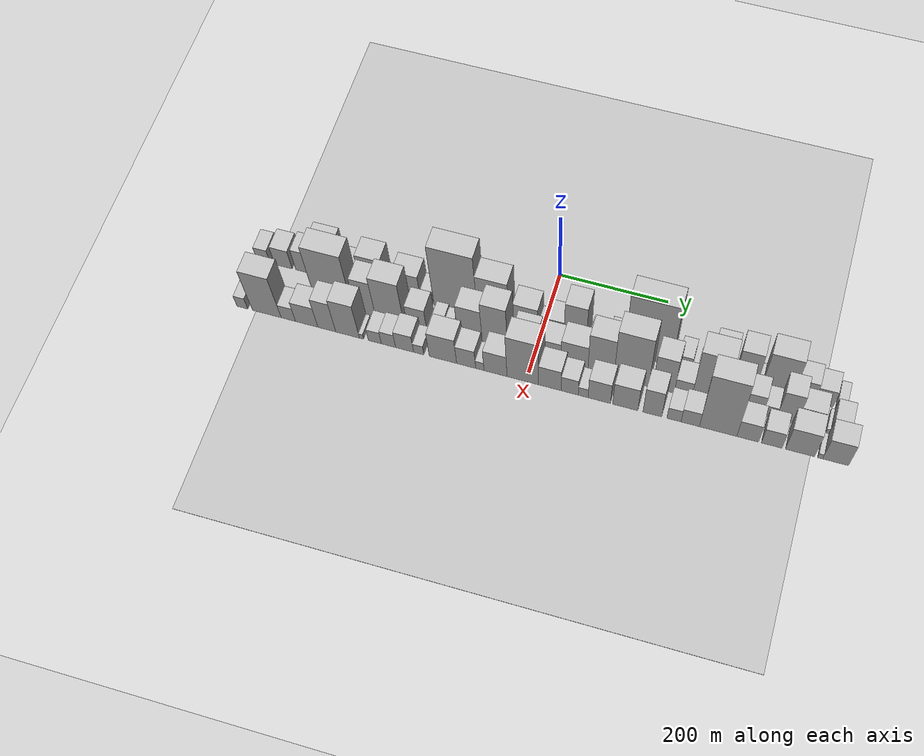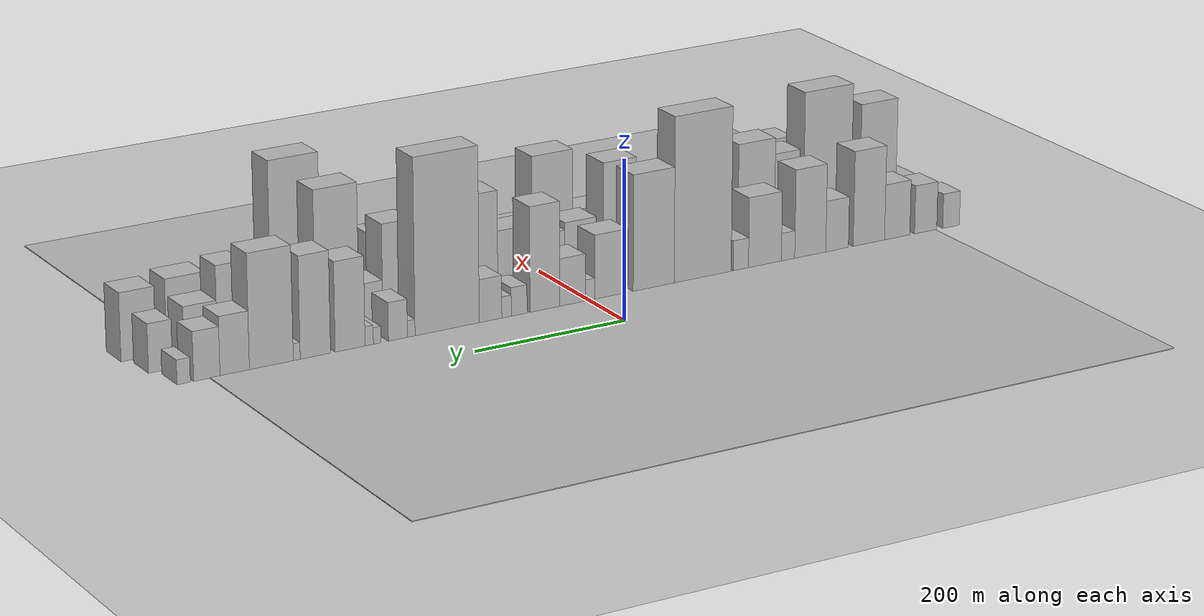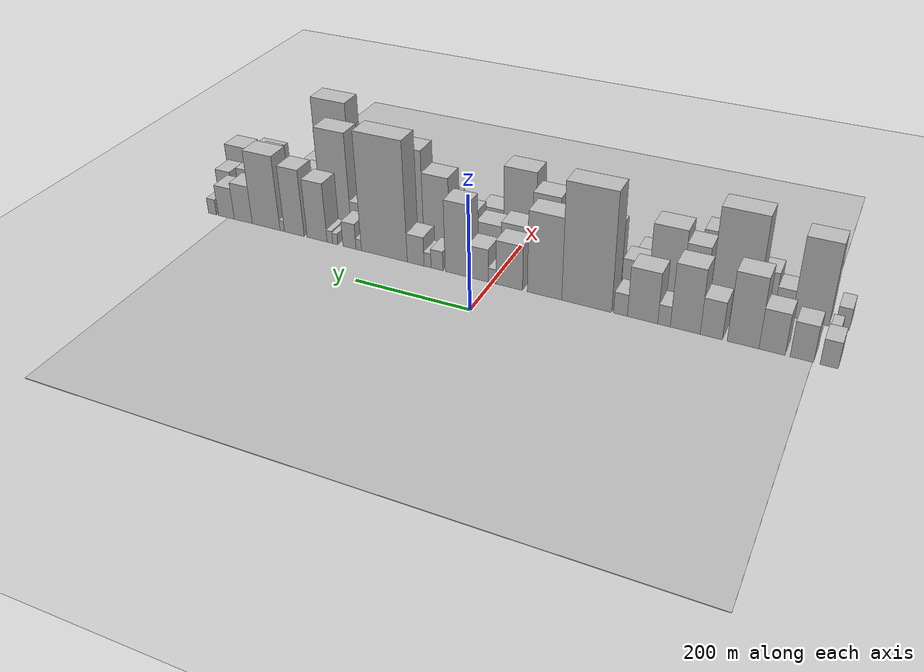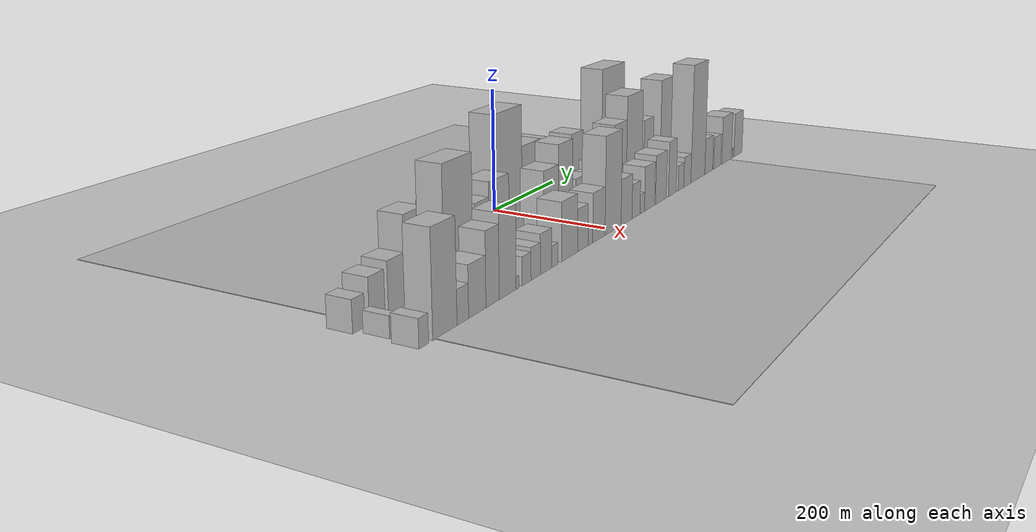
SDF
<?xml version="1.0" encoding="utf-8"?>

<sdf version="1.6">

   <world name="default">

      <gui fullscreen="0">

         <camera name="user_camera">

            <pose>-15 0 4.57585 0 0 0</pose>

            <view_controller>orbit</view_controller>

         </camera>

      </gui>

      <scene>

         <sky>

           <clouds>

             <speed>12</speed>

           </clouds>

         </sky>

         <ambient>0.4 0.4 0.4 1</ambient>

         <background>0.7 0.7 0.7 1</background>

         <shadows>1</shadows>

      </scene>

      <gravity>0 0 -9.8066</gravity>

      <magnetic_field>6e-06 2.3e-05 -4.2e-05</magnetic_field>

      <physics default="0" name="default_physics" type="ode">

         <ode>

            <solver>

               <type>quick</type>

               <iters>10</iters>

               <sor>1.0</sor>

               <use_dynamic_moi_rescaling>0</use_dynamic_moi_rescaling>

            </solver>

            <constraints>

               <cfm>0</cfm>

               <erp>0.2</erp>

               <contact_max_correcting_vel>100</contact_max_correcting_vel>

               <contact_surface_layer>0.001</contact_surface_layer>

            </constraints>

         </ode>

         <max_step_size>0.004</max_step_size>

         <real_time_factor>1</real_time_factor>

         <real_time_update_rate>250</real_time_update_rate>

      </physics>

      <light name="sun" type="directional">

         <cast_shadows>1</cast_shadows>

         <pose>0 0 10 0 0 0</pose>

         <diffuse>0.8 0.8 0.8 1</diffuse>

         <specular>0.2 0.2 0.2 1</specular>

         <attenuation>

            <range>1000</range>

            <constant>0.9</constant>

            <linear>0.01</linear>

            <quadratic>0.001</quadratic>

         </attenuation>

         <direction>-0.5 0.1 -0.9</direction>

      </light>

      <include>

         <name>ground_plane_1</name>

         <uri>model://HANNAS_ground_plane</uri>

         <pose>0 0 0  0 0 0</pose>

      </include>

      <include>

         <name>ground_plane_2</name>

         <uri>model://HANNAS_ground_plane</uri>

         <pose>100 0 0  0 0 0</pose>

      </include>

      <model name="building_1">

         <static>1</static>

         <pose frame="">100.0000 -523.2998 0 0.000000 0.000000 0.000000</pose>

         <link name="link">

            <pose frame="">0 0 22.50 0 0 0</pose>

            <collision name="collision">

               <geometry>

                  <box>

                     <size>40.0000 25.4005 45.0000</size>

                  </box>

               </geometry>

               <max_contacts>10</max_contacts>

               <surface>

                  <contact>

                     <ode/>

                  </contact>

                  <bounce/>

                  <friction>

                     <torsional>

                        <ode/>

                     </torsional>

                     <ode/>

                  </friction>

               </surface>

            </collision>

            <visual name="visual">

               <cast_shadows>0</cast_shadows>

               <geometry>

                  <box>

                     <size>40.0000 25.4005 45.0000</size>

                  </box>

               </geometry>

               <material>

                  <script>

                     <uri>model://HANNAS_wall/materials/scripts</uri>

                     <uri>model://HANNAS_wall/materials/textures</uri>

                     <name>vrc/HANNAS_wall</name>

                  </script>

               </material>

            </visual>

            <self_collide>0</self_collide>

            <enable_wind>0</enable_wind>

            <kinematic>0</kinematic>

         </link>

      </model>

      <model name="building_2">

         <static>1</static>

         <pose frame="">100.0000 -484.8610 0 0.000000 0.000000 0.000000</pose>

         <link name="link">

            <pose frame="">0 0 31.50 0 0 0</pose>

            <collision name="collision">

               <geometry>

                  <box>

                     <size>40.0000 33.4771 63.0000</size>

                  </box>

               </geometry>

               <max_contacts>10</max_contacts>

               <surface>

                  <contact>

                     <ode/>

                  </contact>

                  <bounce/>

                  <friction>

                     <torsional>

                        <ode/>

                     </torsional>

                     <ode/>

                  </friction>

               </surface>

            </collision>

            <visual name="visual">

               <cast_shadows>0</cast_shadows>

               <geometry>

                  <box>

                     <size>40.0000 33.4771 63.0000</size>

                  </box>

               </geometry>

               <material>

                  <script>

                     <uri>model://HANNAS_wall/materials/scripts</uri>

                     <uri>model://HANNAS_wall/materials/textures</uri>

                     <name>vrc/HANNAS_wall</name>

                  </script>

               </material>

            </visual>

            <self_collide>0</self_collide>

            <enable_wind>0</enable_wind>

            <kinematic>0</kinematic>

         </link>

      </model>

      <model name="building_3">

         <static>1</static>

         <pose frame="">100.0000 -442.2301 0 0.000000 0.000000 0.000000</pose>

         <link name="link">

            <pose frame="">0 0 36.00 0 0 0</pose>

            <collision name="collision">

               <geometry>

                  <box>

                     <size>40.0000 37.7847 72.0000</size>

                  </box>

               </geometry>

               <max_contacts>10</max_contacts>

               <surface>

                  <contact>

                     <ode/>

                  </contact>

                  <bounce/>

                  <friction>

                     <torsional>

                        <ode/>

                     </torsional>

                     <ode/>

                  </friction>

               </surface>

            </collision>

            <visual name="visual">

               <cast_shadows>0</cast_shadows>

               <geometry>

                  <box>

                     <size>40.0000 37.7847 72.0000</size>

                  </box>

               </geometry>

               <material>

                  <script>

                     <uri>model://HANNAS_wall/materials/scripts</uri>

                     <uri>model://HANNAS_wall/materials/textures</uri>

                     <name>vrc/HANNAS_wall</name>

                  </script>

               </material>

            </visual>

            <self_collide>0</self_collide>

            <enable_wind>0</enable_wind>

            <kinematic>0</kinematic>

         </link>

      </model>

      <model name="building_4">

         <static>1</static>

         <pose frame="">100.0000 -400.0121 0 0.000000 0.000000 0.000000</pose>

         <link name="link">

            <pose frame="">0 0 61.50 0 0 0</pose>

            <collision name="collision">

               <geometry>

                  <box>

                     <size>40.0000 46.6512 123.0000</size>

                  </box>

               </geometry>

               <max_contacts>10</max_contacts>

               <surface>

                  <contact>

                     <ode/>

                  </contact>

                  <bounce/>

                  <friction>

                     <torsional>

                        <ode/>

                     </torsional>

                     <ode/>

                  </friction>

               </surface>

            </collision>

            <visual name="visual">

               <cast_shadows>0</cast_shadows>

               <geometry>

                  <box>

                     <size>40.0000 46.6512 123.0000</size>

                  </box>

               </geometry>

               <material>

                  <script>

                     <uri>model://HANNAS_wall/materials/scripts</uri>

                     <uri>model://HANNAS_wall/materials/textures</uri>

                     <name>vrc/HANNAS_wall</name>

                  </script>

               </material>

            </visual>

            <self_collide>0</self_collide>

            <enable_wind>0</enable_wind>

            <kinematic>0</kinematic>

         </link>

      </model>

      <model name="building_5">

         <static>1</static>

         <pose frame="">100.0000 -353.0033 0 0.000000 0.000000 0.000000</pose>

         <link name="link">

            <pose frame="">0 0 33.00 0 0 0</pose>

            <collision name="collision">

               <geometry>

                  <box>

                     <size>40.0000 33.3665 66.0000</size>

                  </box>

               </geometry>

               <max_contacts>10</max_contacts>

               <surface>

                  <contact>

                     <ode/>

                  </contact>

                  <bounce/>

                  <friction>

                     <torsional>

                        <ode/>

                     </torsional>

                     <ode/>

                  </friction>

               </surface>

            </collision>

            <visual name="visual">

               <cast_shadows>0</cast_shadows>

               <geometry>

                  <box>

                     <size>40.0000 33.3665 66.0000</size>

                  </box>

               </geometry>

               <material>

                  <script>

                     <uri>model://HANNAS_wall/materials/scripts</uri>

                     <uri>model://HANNAS_wall/materials/textures</uri>

                     <name>vrc/HANNAS_wall</name>

                  </script>

               </material>

            </visual>

            <self_collide>0</self_collide>

            <enable_wind>0</enable_wind>

            <kinematic>0</kinematic>

         </link>

      </model>

      <model name="building_6">

         <static>1</static>

         <pose frame="">100.0000 -313.5647 0 0.000000 0.000000 0.000000</pose>

         <link name="link">

            <pose frame="">0 0 57.00 0 0 0</pose>

            <collision name="collision">

               <geometry>

                  <box>

                     <size>40.0000 45.5107 114.0000</size>

                  </box>

               </geometry>

               <max_contacts>10</max_contacts>

               <surface>

                  <contact>

                     <ode/>

                  </contact>

                  <bounce/>

                  <friction>

                     <torsional>

                        <ode/>

                     </torsional>

                     <ode/>

                  </friction>

               </surface>

            </collision>

            <visual name="visual">

               <cast_shadows>0</cast_shadows>

               <geometry>

                  <box>

                     <size>40.0000 45.5107 114.0000</size>

                  </box>

               </geometry>

               <material>

                  <script>

                     <uri>model://HANNAS_wall/materials/scripts</uri>

                     <uri>model://HANNAS_wall/materials/textures</uri>

                     <name>vrc/HANNAS_wall</name>

                  </script>

               </material>

            </visual>

            <self_collide>0</self_collide>

            <enable_wind>0</enable_wind>

            <kinematic>0</kinematic>

         </link>

      </model>

      <model name="building_7">

         <static>1</static>

         <pose frame="">100.0000 -281.1335 0 0.000000 0.000000 0.000000</pose>

         <link name="link">

            <pose frame="">0 0 18.00 0 0 0</pose>

            <collision name="collision">

               <geometry>

                  <box>

                     <size>40.0000 19.3517 36.0000</size>

                  </box>

               </geometry>

               <max_contacts>10</max_contacts>

               <surface>

                  <contact>

                     <ode/>

                  </contact>

                  <bounce/>

                  <friction>

                     <torsional>

                        <ode/>

                     </torsional>

                     <ode/>

                  </friction>

               </surface>

            </collision>

            <visual name="visual">

               <cast_shadows>0</cast_shadows>

               <geometry>

                  <box>

                     <size>40.0000 19.3517 36.0000</size>

                  </box>

               </geometry>

               <material>

                  <script>

                     <uri>model://HANNAS_wall/materials/scripts</uri>

                     <uri>model://HANNAS_wall/materials/textures</uri>

                     <name>vrc/HANNAS_wall</name>

                  </script>

               </material>

            </visual>

            <self_collide>0</self_collide>

            <enable_wind>0</enable_wind>

            <kinematic>0</kinematic>

         </link>

      </model>

      <model name="building_8">

         <static>1</static>

         <pose frame="">100.0000 -247.7661 0 0.000000 0.000000 0.000000</pose>

         <link name="link">

            <pose frame="">0 0 45.00 0 0 0</pose>

            <collision name="collision">

               <geometry>

                  <box>

                     <size>40.0000 47.3833 90.0000</size>

                  </box>

               </geometry>

               <max_contacts>10</max_contacts>

               <surface>

                  <contact>

                     <ode/>

                  </contact>

                  <bounce/>

                  <friction>

                     <torsional>

                        <ode/>

                     </torsional>

                     <ode/>

                  </friction>

               </surface>

            </collision>

            <visual name="visual">

               <cast_shadows>0</cast_shadows>

               <geometry>

                  <box>

                     <size>40.0000 47.3833 90.0000</size>

                  </box>

               </geometry>

               <material>

                  <script>

                     <uri>model://HANNAS_wall/materials/scripts</uri>

                     <uri>model://HANNAS_wall/materials/textures</uri>

                     <name>vrc/HANNAS_wall</name>

                  </script>

               </material>

            </visual>

            <self_collide>0</self_collide>

            <enable_wind>0</enable_wind>

            <kinematic>0</kinematic>

         </link>

      </model>

      <model name="building_9">

         <static>1</static>

         <pose frame="">100.0000 -213.0983 0 0.000000 0.000000 0.000000</pose>

         <link name="link">

            <pose frame="">0 0 19.50 0 0 0</pose>

            <collision name="collision">

               <geometry>

                  <box>

                     <size>40.0000 21.9523 39.0000</size>

                  </box>

               </geometry>

               <max_contacts>10</max_contacts>

               <surface>

                  <contact>

                     <ode/>

                  </contact>

                  <bounce/>

                  <friction>

                     <torsional>

                        <ode/>

                     </torsional>

                     <ode/>

                  </friction>

               </surface>

            </collision>

            <visual name="visual">

               <cast_shadows>0</cast_shadows>

               <geometry>

                  <box>

                     <size>40.0000 21.9523 39.0000</size>

                  </box>

               </geometry>

               <material>

                  <script>

                     <uri>model://HANNAS_wall/materials/scripts</uri>

                     <uri>model://HANNAS_wall/materials/textures</uri>

                     <name>vrc/HANNAS_wall</name>

                  </script>

               </material>

            </visual>

            <self_collide>0</self_collide>

            <enable_wind>0</enable_wind>

            <kinematic>0</kinematic>

         </link>

      </model>

      <model name="building_10">

         <static>1</static>

         <pose frame="">100.0000 -158.5872 0 0.000000 0.000000 0.000000</pose>

         <link name="link">

            <pose frame="">0 0 105.00 0 0 0</pose>

            <collision name="collision">

               <geometry>

                  <box>

                     <size>40.0000 81.0699 210.0000</size>

                  </box>

               </geometry>

               <max_contacts>10</max_contacts>

               <surface>

                  <contact>

                     <ode/>

                  </contact>

                  <bounce/>

                  <friction>

                     <torsional>

                        <ode/>

                     </torsional>

                     <ode/>

                  </friction>

               </surface>

            </collision>

            <visual name="visual">

               <cast_shadows>0</cast_shadows>

               <geometry>

                  <box>

                     <size>40.0000 81.0699 210.0000</size>

                  </box>

               </geometry>

               <material>

                  <script>

                     <uri>model://HANNAS_wall/materials/scripts</uri>

                     <uri>model://HANNAS_wall/materials/textures</uri>

                     <name>vrc/HANNAS_wall</name>

                  </script>

               </material>

            </visual>

            <self_collide>0</self_collide>

            <enable_wind>0</enable_wind>

            <kinematic>0</kinematic>

         </link>

      </model>

      <model name="building_11">

         <static>1</static>

         <pose frame="">100.0000 -89.3004 0 0.000000 0.000000 0.000000</pose>

         <link name="link">

            <pose frame="">0 0 73.50 0 0 0</pose>

            <collision name="collision">

               <geometry>

                  <box>

                     <size>40.0000 57.5038 147.0000</size>

                  </box>

               </geometry>

               <max_contacts>10</max_contacts>

               <surface>

                  <contact>

                     <ode/>

                  </contact>

                  <bounce/>

                  <friction>

                     <torsional>

                        <ode/>

                     </torsional>

                     <ode/>

                  </friction>

               </surface>

            </collision>

            <visual name="visual">

               <cast_shadows>0</cast_shadows>

               <geometry>

                  <box>

                     <size>40.0000 57.5038 147.0000</size>

                  </box>

               </geometry>

               <material>

                  <script>

                     <uri>model://HANNAS_wall/materials/scripts</uri>

                     <uri>model://HANNAS_wall/materials/textures</uri>

                     <name>vrc/HANNAS_wall</name>

                  </script>

               </material>

            </visual>

            <self_collide>0</self_collide>

            <enable_wind>0</enable_wind>

            <kinematic>0</kinematic>

         </link>

      </model>

      <model name="building_12">

         <static>1</static>

         <pose frame="">100.0000 -29.7991 0 0.000000 0.000000 0.000000</pose>

         <link name="link">

            <pose frame="">0 0 40.50 0 0 0</pose>

            <collision name="collision">

               <geometry>

                  <box>

                     <size>40.0000 45.4987 81.0000</size>

                  </box>

               </geometry>

               <max_contacts>10</max_contacts>

               <surface>

                  <contact>

                     <ode/>

                  </contact>

                  <bounce/>

                  <friction>

                     <torsional>

                        <ode/>

                     </torsional>

                     <ode/>

                  </friction>

               </surface>

            </collision>

            <visual name="visual">

               <cast_shadows>0</cast_shadows>

               <geometry>

                  <box>

                     <size>40.0000 45.4987 81.0000</size>

                  </box>

               </geometry>

               <material>

                  <script>

                     <uri>model://HANNAS_wall/materials/scripts</uri>

                     <uri>model://HANNAS_wall/materials/textures</uri>

                     <name>vrc/HANNAS_wall</name>

                  </script>

               </material>

            </visual>

            <self_collide>0</self_collide>

            <enable_wind>0</enable_wind>

            <kinematic>0</kinematic>

         </link>

      </model>

      <model name="building_13">

         <static>1</static>

         <pose frame="">100.0000 -0.4516 0 0.000000 0.000000 0.000000</pose>

         <link name="link">

            <pose frame="">0 0 13.50 0 0 0</pose>

            <collision name="collision">

               <geometry>

                  <box>

                     <size>40.0000 13.1964 27.0000</size>

                  </box>

               </geometry>

               <max_contacts>10</max_contacts>

               <surface>

                  <contact>

                     <ode/>

                  </contact>

                  <bounce/>

                  <friction>

                     <torsional>

                        <ode/>

                     </torsional>

                     <ode/>

                  </friction>

               </surface>

            </collision>

            <visual name="visual">

               <cast_shadows>0</cast_shadows>

               <geometry>

                  <box>

                     <size>40.0000 13.1964 27.0000</size>

                  </box>

               </geometry>

               <material>

                  <script>

                     <uri>model://HANNAS_wall/materials/scripts</uri>

                     <uri>model://HANNAS_wall/materials/textures</uri>

                     <name>vrc/HANNAS_wall</name>

                  </script>

               </material>

            </visual>

            <self_collide>0</self_collide>

            <enable_wind>0</enable_wind>

            <kinematic>0</kinematic>

         </link>

      </model>

      <model name="building_14">

         <static>1</static>

         <pose frame="">100.0000 23.7099 0 0.000000 0.000000 0.000000</pose>

         <link name="link">

            <pose frame="">0 0 30.00 0 0 0</pose>

            <collision name="collision">

               <geometry>

                  <box>

                     <size>40.0000 35.1267 60.0000</size>

                  </box>

               </geometry>

               <max_contacts>10</max_contacts>

               <surface>

                  <contact>

                     <ode/>

                  </contact>

                  <bounce/>

                  <friction>

                     <torsional>

                        <ode/>

                     </torsional>

                     <ode/>

                  </friction>

               </surface>

            </collision>

            <visual name="visual">

               <cast_shadows>0</cast_shadows>

               <geometry>

                  <box>

                     <size>40.0000 35.1267 60.0000</size>

                  </box>

               </geometry>

               <material>

                  <script>

                     <uri>model://HANNAS_wall/materials/scripts</uri>

                     <uri>model://HANNAS_wall/materials/textures</uri>

                     <name>vrc/HANNAS_wall</name>

                  </script>

               </material>

            </visual>

            <self_collide>0</self_collide>

            <enable_wind>0</enable_wind>

            <kinematic>0</kinematic>

         </link>

      </model>

      <model name="building_15">

         <static>1</static>

         <pose frame="">100.0000 61.4964 0 0.000000 0.000000 0.000000</pose>

         <link name="link">

            <pose frame="">0 0 66.00 0 0 0</pose>

            <collision name="collision">

               <geometry>

                  <box>

                     <size>40.0000 40.4464 132.0000</size>

                  </box>

               </geometry>

               <max_contacts>10</max_contacts>

               <surface>

                  <contact>

                     <ode/>

                  </contact>

                  <bounce/>

                  <friction>

                     <torsional>

                        <ode/>

                     </torsional>

                     <ode/>

                  </friction>

               </surface>

            </collision>

            <visual name="visual">

               <cast_shadows>0</cast_shadows>

               <geometry>

                  <box>

                     <size>40.0000 40.4464 132.0000</size>

                  </box>

               </geometry>

               <material>

                  <script>

                     <uri>model://HANNAS_wall/materials/scripts</uri>

                     <uri>model://HANNAS_wall/materials/textures</uri>

                     <name>vrc/HANNAS_wall</name>

                  </script>

               </material>

            </visual>

            <self_collide>0</self_collide>

            <enable_wind>0</enable_wind>

            <kinematic>0</kinematic>

         </link>

      </model>

      <model name="building_16">

         <static>1</static>

         <pose frame="">100.0000 96.4105 0 0.000000 0.000000 0.000000</pose>

         <link name="link">

            <pose frame="">0 0 18.00 0 0 0</pose>

            <collision name="collision">

               <geometry>

                  <box>

                     <size>40.0000 21.3817 36.0000</size>

                  </box>

               </geometry>

               <max_contacts>10</max_contacts>

               <surface>

                  <contact>

                     <ode/>

                  </contact>

                  <bounce/>

                  <friction>

                     <torsional>

                        <ode/>

                     </torsional>

                     <ode/>

                  </friction>

               </surface>

            </collision>

            <visual name="visual">

               <cast_shadows>0</cast_shadows>

               <geometry>

                  <box>

                     <size>40.0000 21.3817 36.0000</size>

                  </box>

               </geometry>

               <material>

                  <script>

                     <uri>model://HANNAS_wall/materials/scripts</uri>

                     <uri>model://HANNAS_wall/materials/textures</uri>

                     <name>vrc/HANNAS_wall</name>

                  </script>

               </material>

            </visual>

            <self_collide>0</self_collide>

            <enable_wind>0</enable_wind>

            <kinematic>0</kinematic>

         </link>

      </model>

      <model name="building_17">

         <static>1</static>

         <pose frame="">100.0000 113.4703 0 0.000000 0.000000 0.000000</pose>

         <link name="link">

            <pose frame="">0 0 13.50 0 0 0</pose>

            <collision name="collision">

               <geometry>

                  <box>

                     <size>40.0000 12.7378 27.0000</size>

                  </box>

               </geometry>

               <max_contacts>10</max_contacts>

               <surface>

                  <contact>

                     <ode/>

                  </contact>

                  <bounce/>

                  <friction>

                     <torsional>

                        <ode/>

                     </torsional>

                     <ode/>

                  </friction>

               </surface>

            </collision>

            <visual name="visual">

               <cast_shadows>0</cast_shadows>

               <geometry>

                  <box>

                     <size>40.0000 12.7378 27.0000</size>

                  </box>

               </geometry>

               <material>

                  <script>

                     <uri>model://HANNAS_wall/materials/scripts</uri>

                     <uri>model://HANNAS_wall/materials/textures</uri>

                     <name>vrc/HANNAS_wall</name>

                  </script>

               </material>

            </visual>

            <self_collide>0</self_collide>

            <enable_wind>0</enable_wind>

            <kinematic>0</kinematic>

         </link>

      </model>

      <model name="building_18">

         <static>1</static>

         <pose frame="">100.0000 135.0646 0 0.000000 0.000000 0.000000</pose>

         <link name="link">

            <pose frame="">0 0 27.00 0 0 0</pose>

            <collision name="collision">

               <geometry>

                  <box>

                     <size>40.0000 30.4509 54.0000</size>

                  </box>

               </geometry>

               <max_contacts>10</max_contacts>

               <surface>

                  <contact>

                     <ode/>

                  </contact>

                  <bounce/>

                  <friction>

                     <torsional>

                        <ode/>

                     </torsional>

                     <ode/>

                  </friction>

               </surface>

            </collision>

            <visual name="visual">

               <cast_shadows>0</cast_shadows>

               <geometry>

                  <box>

                     <size>40.0000 30.4509 54.0000</size>

                  </box>

               </geometry>

               <material>

                  <script>

                     <uri>model://HANNAS_wall/materials/scripts</uri>

                     <uri>model://HANNAS_wall/materials/textures</uri>

                     <name>vrc/HANNAS_wall</name>

                  </script>

               </material>

            </visual>

            <self_collide>0</self_collide>

            <enable_wind>0</enable_wind>

            <kinematic>0</kinematic>

         </link>

      </model>

      <model name="building_19">

         <static>1</static>

         <pose frame="">100.0000 193.0504 0 0.000000 0.000000 0.000000</pose>

         <link name="link">

            <pose frame="">0 0 109.50 0 0 0</pose>

            <collision name="collision">

               <geometry>

                  <box>

                     <size>40.0000 85.5208 219.0000</size>

                  </box>

               </geometry>

               <max_contacts>10</max_contacts>

               <surface>

                  <contact>

                     <ode/>

                  </contact>

                  <bounce/>

                  <friction>

                     <torsional>

                        <ode/>

                     </torsional>

                     <ode/>

                  </friction>

               </surface>

            </collision>

            <visual name="visual">

               <cast_shadows>0</cast_shadows>

               <geometry>

                  <box>

                     <size>40.0000 85.5208 219.0000</size>

                  </box>

               </geometry>

               <material>

                  <script>

                     <uri>model://HANNAS_wall/materials/scripts</uri>

                     <uri>model://HANNAS_wall/materials/textures</uri>

                     <name>vrc/HANNAS_wall</name>

                  </script>

               </material>

            </visual>

            <self_collide>0</self_collide>

            <enable_wind>0</enable_wind>

            <kinematic>0</kinematic>

         </link>

      </model>

      <model name="building_20">

         <static>1</static>

         <pose frame="">100.0000 240.8615 0 0.000000 0.000000 0.000000</pose>

         <link name="link">

            <pose frame="">0 0 10.50 0 0 0</pose>

            <collision name="collision">

               <geometry>

                  <box>

                     <size>40.0000 10.1014 21.0000</size>

                  </box>

               </geometry>

               <max_contacts>10</max_contacts>

               <surface>

                  <contact>

                     <ode/>

                  </contact>

                  <bounce/>

                  <friction>

                     <torsional>

                        <ode/>

                     </torsional>

                     <ode/>

                  </friction>

               </surface>

            </collision>

            <visual name="visual">

               <cast_shadows>0</cast_shadows>

               <geometry>

                  <box>

                     <size>40.0000 10.1014 21.0000</size>

                  </box>

               </geometry>

               <material>

                  <script>

                     <uri>model://HANNAS_wall/materials/scripts</uri>

                     <uri>model://HANNAS_wall/materials/textures</uri>

                     <name>vrc/HANNAS_wall</name>

                  </script>

               </material>

            </visual>

            <self_collide>0</self_collide>

            <enable_wind>0</enable_wind>

            <kinematic>0</kinematic>

         </link>

      </model>

      <model name="building_21">

         <static>1</static>

         <pose frame="">100.0000 258.3978 0 0.000000 0.000000 0.000000</pose>

         <link name="link">

            <pose frame="">0 0 24.00 0 0 0</pose>

            <collision name="collision">

               <geometry>

                  <box>

                     <size>40.0000 24.9711 48.0000</size>

                  </box>

               </geometry>

               <max_contacts>10</max_contacts>

               <surface>

                  <contact>

                     <ode/>

                  </contact>

                  <bounce/>

                  <friction>

                     <torsional>

                        <ode/>

                     </torsional>

                     <ode/>

                  </friction>

               </surface>

            </collision>

            <visual name="visual">

               <cast_shadows>0</cast_shadows>

               <geometry>

                  <box>

                     <size>40.0000 24.9711 48.0000</size>

                  </box>

               </geometry>

               <material>

                  <script>

                     <uri>model://HANNAS_wall/materials/scripts</uri>

                     <uri>model://HANNAS_wall/materials/textures</uri>

                     <name>vrc/HANNAS_wall</name>

                  </script>

               </material>

            </visual>

            <self_collide>0</self_collide>

            <enable_wind>0</enable_wind>

            <kinematic>0</kinematic>

         </link>

      </model>

      <model name="building_22">

         <static>1</static>

         <pose frame="">100.0000 285.7447 0 0.000000 0.000000 0.000000</pose>

         <link name="link">

            <pose frame="">0 0 10.50 0 0 0</pose>

            <collision name="collision">

               <geometry>

                  <box>

                     <size>40.0000 9.7227 21.0000</size>

                  </box>

               </geometry>

               <max_contacts>10</max_contacts>

               <surface>

                  <contact>

                     <ode/>

                  </contact>

                  <bounce/>

                  <friction>

                     <torsional>

                        <ode/>

                     </torsional>

                     <ode/>

                  </friction>

               </surface>

            </collision>

            <visual name="visual">

               <cast_shadows>0</cast_shadows>

               <geometry>

                  <box>

                     <size>40.0000 9.7227 21.0000</size>

                  </box>

               </geometry>

               <material>

                  <script>

                     <uri>model://HANNAS_wall/materials/scripts</uri>

                     <uri>model://HANNAS_wall/materials/textures</uri>

                     <name>vrc/HANNAS_wall</name>

                  </script>

               </material>

            </visual>

            <self_collide>0</self_collide>

            <enable_wind>0</enable_wind>

            <kinematic>0</kinematic>

         </link>

      </model>

      <model name="building_23">

         <static>1</static>

         <pose frame="">100.0000 296.0461 0 0.000000 0.000000 0.000000</pose>

         <link name="link">

            <pose frame="">0 0 12.00 0 0 0</pose>

            <collision name="collision">

               <geometry>

                  <box>

                     <size>40.0000 10.8802 24.0000</size>

                  </box>

               </geometry>

               <max_contacts>10</max_contacts>

               <surface>

                  <contact>

                     <ode/>

                  </contact>

                  <bounce/>

                  <friction>

                     <torsional>

                        <ode/>

                     </torsional>

                     <ode/>

                  </friction>

               </surface>

            </collision>

            <visual name="visual">

               <cast_shadows>0</cast_shadows>

               <geometry>

                  <box>

                     <size>40.0000 10.8802 24.0000</size>

                  </box>

               </geometry>

               <material>

                  <script>

                     <uri>model://HANNAS_wall/materials/scripts</uri>

                     <uri>model://HANNAS_wall/materials/textures</uri>

                     <name>vrc/HANNAS_wall</name>

                  </script>

               </material>

            </visual>

            <self_collide>0</self_collide>

            <enable_wind>0</enable_wind>

            <kinematic>0</kinematic>

         </link>

      </model>

      <model name="building_24">

         <static>1</static>

         <pose frame="">100.0000 320.9167 0 0.000000 0.000000 0.000000</pose>

         <link name="link">

            <pose frame="">0 0 55.50 0 0 0</pose>

            <collision name="collision">

               <geometry>

                  <box>

                     <size>40.0000 38.8610 111.0000</size>

                  </box>

               </geometry>

               <max_contacts>10</max_contacts>

               <surface>

                  <contact>

                     <ode/>

                  </contact>

                  <bounce/>

                  <friction>

                     <torsional>

                        <ode/>

                     </torsional>

                     <ode/>

                  </friction>

               </surface>

            </collision>

            <visual name="visual">

               <cast_shadows>0</cast_shadows>

               <geometry>

                  <box>

                     <size>40.0000 38.8610 111.0000</size>

                  </box>

               </geometry>

               <material>

                  <script>

                     <uri>model://HANNAS_wall/materials/scripts</uri>

                     <uri>model://HANNAS_wall/materials/textures</uri>

                     <name>vrc/HANNAS_wall</name>

                  </script>

               </material>

            </visual>

            <self_collide>0</self_collide>

            <enable_wind>0</enable_wind>

            <kinematic>0</kinematic>

         </link>

      </model>

      <model name="building_25">

         <static>1</static>

         <pose frame="">100.0000 365.8912 0 0.000000 0.000000 0.000000</pose>

         <link name="link">

            <pose frame="">0 0 63.00 0 0 0</pose>

            <collision name="collision">

               <geometry>

                  <box>

                     <size>40.0000 39.0881 126.0000</size>

                  </box>

               </geometry>

               <max_contacts>10</max_contacts>

               <surface>

                  <contact>

                     <ode/>

                  </contact>

                  <bounce/>

                  <friction>

                     <torsional>

                        <ode/>

                     </torsional>

                     <ode/>

                  </friction>

               </surface>

            </collision>

            <visual name="visual">

               <cast_shadows>0</cast_shadows>

               <geometry>

                  <box>

                     <size>40.0000 39.0881 126.0000</size>

                  </box>

               </geometry>

               <material>

                  <script>

                     <uri>model://HANNAS_wall/materials/scripts</uri>

                     <uri>model://HANNAS_wall/materials/textures</uri>

                     <name>vrc/HANNAS_wall</name>

                  </script>

               </material>

            </visual>

            <self_collide>0</self_collide>

            <enable_wind>0</enable_wind>

            <kinematic>0</kinematic>

         </link>

      </model>

      <model name="building_26">

         <static>1</static>

         <pose frame="">100.0000 389.8815 0 0.000000 0.000000 0.000000</pose>

         <link name="link">

            <pose frame="">0 0 10.50 0 0 0</pose>

            <collision name="collision">

               <geometry>

                  <box>

                     <size>40.0000 8.8925 21.0000</size>

                  </box>

               </geometry>

               <max_contacts>10</max_contacts>

               <surface>

                  <contact>

                     <ode/>

                  </contact>

                  <bounce/>

                  <friction>

                     <torsional>

                        <ode/>

                     </torsional>

                     <ode/>

                  </friction>

               </surface>

            </collision>

            <visual name="visual">

               <cast_shadows>0</cast_shadows>

               <geometry>

                  <box>

                     <size>40.0000 8.8925 21.0000</size>

                  </box>

               </geometry>

               <material>

                  <script>

                     <uri>model://HANNAS_wall/materials/scripts</uri>

                     <uri>model://HANNAS_wall/materials/textures</uri>

                     <name>vrc/HANNAS_wall</name>

                  </script>

               </material>

            </visual>

            <self_collide>0</self_collide>

            <enable_wind>0</enable_wind>

            <kinematic>0</kinematic>

         </link>

      </model>

      <model name="building_27">

         <static>1</static>

         <pose frame="">100.0000 422.3548 0 0.000000 0.000000 0.000000</pose>

         <link name="link">

            <pose frame="">0 0 70.50 0 0 0</pose>

            <collision name="collision">

               <geometry>

                  <box>

                     <size>40.0000 56.0541 141.0000</size>

                  </box>

               </geometry>

               <max_contacts>10</max_contacts>

               <surface>

                  <contact>

                     <ode/>

                  </contact>

                  <bounce/>

                  <friction>

                     <torsional>

                        <ode/>

                     </torsional>

                     <ode/>

                  </friction>

               </surface>

            </collision>

            <visual name="visual">

               <cast_shadows>0</cast_shadows>

               <geometry>

                  <box>

                     <size>40.0000 56.0541 141.0000</size>

                  </box>

               </geometry>

               <material>

                  <script>

                     <uri>model://HANNAS_wall/materials/scripts</uri>

                     <uri>model://HANNAS_wall/materials/textures</uri>

                     <name>vrc/HANNAS_wall</name>

                  </script>

               </material>

            </visual>

            <self_collide>0</self_collide>

            <enable_wind>0</enable_wind>

            <kinematic>0</kinematic>

         </link>

      </model>

      <model name="building_28">

         <static>1</static>

         <pose frame="">100.0000 468.9450 0 0.000000 0.000000 0.000000</pose>

         <link name="link">

            <pose frame="">0 0 36.00 0 0 0</pose>

            <collision name="collision">

               <geometry>

                  <box>

                     <size>40.0000 37.1263 72.0000</size>

                  </box>

               </geometry>

               <max_contacts>10</max_contacts>

               <surface>

                  <contact>

                     <ode/>

                  </contact>

                  <bounce/>

                  <friction>

                     <torsional>

                        <ode/>

                     </torsional>

                     <ode/>

                  </friction>

               </surface>

            </collision>

            <visual name="visual">

               <cast_shadows>0</cast_shadows>

               <geometry>

                  <box>

                     <size>40.0000 37.1263 72.0000</size>

                  </box>

               </geometry>

               <material>

                  <script>

                     <uri>model://HANNAS_wall/materials/scripts</uri>

                     <uri>model://HANNAS_wall/materials/textures</uri>

                     <name>vrc/HANNAS_wall</name>

                  </script>

               </material>

            </visual>

            <self_collide>0</self_collide>

            <enable_wind>0</enable_wind>

            <kinematic>0</kinematic>

         </link>

      </model>

      <model name="building_29">

         <static>1</static>

         <pose frame="">100.0000 504.1079 0 0.000000 0.000000 0.000000</pose>

         <link name="link">

            <pose frame="">0 0 30.00 0 0 0</pose>

            <collision name="collision">

               <geometry>

                  <box>

                     <size>40.0000 33.1996 60.0000</size>

                  </box>

               </geometry>

               <max_contacts>10</max_contacts>

               <surface>

                  <contact>

                     <ode/>

                  </contact>

                  <bounce/>

                  <friction>

                     <torsional>

                        <ode/>

                     </torsional>

                     <ode/>

                  </friction>

               </surface>

            </collision>

            <visual name="visual">

               <cast_shadows>0</cast_shadows>

               <geometry>

                  <box>

                     <size>40.0000 33.1996 60.0000</size>

                  </box>

               </geometry>

               <material>

                  <script>

                     <uri>model://HANNAS_wall/materials/scripts</uri>

                     <uri>model://HANNAS_wall/materials/textures</uri>

                     <name>vrc/HANNAS_wall</name>

                  </script>

               </material>

            </visual>

            <self_collide>0</self_collide>

            <enable_wind>0</enable_wind>

            <kinematic>0</kinematic>

         </link>

      </model>

      <model name="building_30">

         <static>1</static>

         <pose frame="">100.0000 533.0738 0 0.000000 0.000000 0.000000</pose>

         <link name="link">

            <pose frame="">0 0 15.00 0 0 0</pose>

            <collision name="collision">

               <geometry>

                  <box>

                     <size>40.0000 16.7322 30.0000</size>

                  </box>

               </geometry>

               <max_contacts>10</max_contacts>

               <surface>

                  <contact>

                     <ode/>

                  </contact>

                  <bounce/>

                  <friction>

                     <torsional>

                        <ode/>

                     </torsional>

                     <ode/>

                  </friction>

               </surface>

            </collision>

            <visual name="visual">

               <cast_shadows>0</cast_shadows>

               <geometry>

                  <box>

                     <size>40.0000 16.7322 30.0000</size>

                  </box>

               </geometry>

               <material>

                  <script>

                     <uri>model://HANNAS_wall/materials/scripts</uri>

                     <uri>model://HANNAS_wall/materials/textures</uri>

                     <name>vrc/HANNAS_wall</name>

                  </script>

               </material>

            </visual>

            <self_collide>0</self_collide>

            <enable_wind>0</enable_wind>

            <kinematic>0</kinematic>

         </link>

      </model>

      <model name="building_31">

         <static>1</static>

         <pose frame="">149.0000 -519.1683 0 0.000000 0.000000 0.000000</pose>

         <link name="link">

            <pose frame="">0 0 15.00 0 0 0</pose>

            <collision name="collision">

               <geometry>

                  <box>

                     <size>40.0000 15.6635 30.0000</size>

                  </box>

               </geometry>

               <max_contacts>10</max_contacts>

               <surface>

                  <contact>

                     <ode/>

                  </contact>

                  <bounce/>

                  <friction>

                     <torsional>

                        <ode/>

                     </torsional>

                     <ode/>

                  </friction>

               </surface>

            </collision>

            <visual name="visual">

               <cast_shadows>0</cast_shadows>

               <geometry>

                  <box>

                     <size>40.0000 15.6635 30.0000</size>

                  </box>

               </geometry>

               <material>

                  <script>

                     <uri>model://HANNAS_wall/materials/scripts</uri>

                     <uri>model://HANNAS_wall/materials/textures</uri>

                     <name>vrc/HANNAS_wall</name>

                  </script>

               </material>

            </visual>

            <self_collide>0</self_collide>

            <enable_wind>0</enable_wind>

            <kinematic>0</kinematic>

         </link>

      </model>

      <model name="building_32">

         <static>1</static>

         <pose frame="">149.0000 -370.2662 0 0.000000 0.000000 0.000000</pose>

         <link name="link">

            <pose frame="">0 0 96.00 0 0 0</pose>

            <collision name="collision">

               <geometry>

                  <box>

                     <size>40.0000 70.7136 192.0000</size>

                  </box>

               </geometry>

               <max_contacts>10</max_contacts>

               <surface>

                  <contact>

                     <ode/>

                  </contact>

                  <bounce/>

                  <friction>

                     <torsional>

                        <ode/>

                     </torsional>

                     <ode/>

                  </friction>

               </surface>

            </collision>

            <visual name="visual">

               <cast_shadows>0</cast_shadows>

               <geometry>

                  <box>

                     <size>40.0000 70.7136 192.0000</size>

                  </box>

               </geometry>

               <material>

                  <script>

                     <uri>model://HANNAS_wall/materials/scripts</uri>

                     <uri>model://HANNAS_wall/materials/textures</uri>

                     <name>vrc/HANNAS_wall</name>

                  </script>

               </material>

            </visual>

            <self_collide>0</self_collide>

            <enable_wind>0</enable_wind>

            <kinematic>0</kinematic>

         </link>

      </model>

      <model name="building_33">

         <static>1</static>

         <pose frame="">149.0000 -310.7645 0 0.000000 0.000000 0.000000</pose>

         <link name="link">

            <pose frame="">0 0 60.00 0 0 0</pose>

            <collision name="collision">

               <geometry>

                  <box>

                     <size>40.0000 36.2898 120.0000</size>

                  </box>

               </geometry>

               <max_contacts>10</max_contacts>

               <surface>

                  <contact>

                     <ode/>

                  </contact>

                  <bounce/>

                  <friction>

                     <torsional>

                        <ode/>

                     </torsional>

                     <ode/>

                  </friction>

               </surface>

            </collision>

            <visual name="visual">

               <cast_shadows>0</cast_shadows>

               <geometry>

                  <box>

                     <size>40.0000 36.2898 120.0000</size>

                  </box>

               </geometry>

               <material>

                  <script>

                     <uri>model://HANNAS_wall/materials/scripts</uri>

                     <uri>model://HANNAS_wall/materials/textures</uri>

                     <name>vrc/HANNAS_wall</name>

                  </script>

               </material>

            </visual>

            <self_collide>0</self_collide>

            <enable_wind>0</enable_wind>

            <kinematic>0</kinematic>

         </link>

      </model>

      <model name="building_34">

         <static>1</static>

         <pose frame="">149.0000 -266.1342 0 0.000000 0.000000 0.000000</pose>

         <link name="link">

            <pose frame="">0 0 70.50 0 0 0</pose>

            <collision name="collision">

               <geometry>

                  <box>

                     <size>40.0000 52.9707 141.0000</size>

                  </box>

               </geometry>

               <max_contacts>10</max_contacts>

               <surface>

                  <contact>

                     <ode/>

                  </contact>

                  <bounce/>

                  <friction>

                     <torsional>

                        <ode/>

                     </torsional>

                     <ode/>

                  </friction>

               </surface>

            </collision>

            <visual name="visual">

               <cast_shadows>0</cast_shadows>

               <geometry>

                  <box>

                     <size>40.0000 52.9707 141.0000</size>

                  </box>

               </geometry>

               <material>

                  <script>

                     <uri>model://HANNAS_wall/materials/scripts</uri>

                     <uri>model://HANNAS_wall/materials/textures</uri>

                     <name>vrc/HANNAS_wall</name>

                  </script>

               </material>

            </visual>

            <self_collide>0</self_collide>

            <enable_wind>0</enable_wind>

            <kinematic>0</kinematic>

         </link>

      </model>

      <model name="building_35">

         <static>1</static>

         <pose frame="">149.0000 -215.5051 0 0.000000 0.000000 0.000000</pose>

         <link name="link">

            <pose frame="">0 0 34.50 0 0 0</pose>

            <collision name="collision">

               <geometry>

                  <box>

                     <size>40.0000 36.2876 69.0000</size>

                  </box>

               </geometry>

               <max_contacts>10</max_contacts>

               <surface>

                  <contact>

                     <ode/>

                  </contact>

                  <bounce/>

                  <friction>

                     <torsional>

                        <ode/>

                     </torsional>

                     <ode/>

                  </friction>

               </surface>

            </collision>

            <visual name="visual">

               <cast_shadows>0</cast_shadows>

               <geometry>

                  <box>

                     <size>40.0000 36.2876 69.0000</size>

                  </box>

               </geometry>

               <material>

                  <script>

                     <uri>model://HANNAS_wall/materials/scripts</uri>

                     <uri>model://HANNAS_wall/materials/textures</uri>

                     <name>vrc/HANNAS_wall</name>

                  </script>

               </material>

            </visual>

            <self_collide>0</self_collide>

            <enable_wind>0</enable_wind>

            <kinematic>0</kinematic>

         </link>

      </model>

      <model name="building_36">

         <static>1</static>

         <pose frame="">149.0000 -177.1518 0 0.000000 0.000000 0.000000</pose>

         <link name="link">

            <pose frame="">0 0 19.50 0 0 0</pose>

            <collision name="collision">

               <geometry>

                  <box>

                     <size>40.0000 22.4188 39.0000</size>

                  </box>

               </geometry>

               <max_contacts>10</max_contacts>

               <surface>

                  <contact>

                     <ode/>

                  </contact>

                  <bounce/>

                  <friction>

                     <torsional>

                        <ode/>

                     </torsional>

                     <ode/>

                  </friction>

               </surface>

            </collision>

            <visual name="visual">

               <cast_shadows>0</cast_shadows>

               <geometry>

                  <box>

                     <size>40.0000 22.4188 39.0000</size>

                  </box>

               </geometry>

               <material>

                  <script>

                     <uri>model://HANNAS_wall/materials/scripts</uri>

                     <uri>model://HANNAS_wall/materials/textures</uri>

                     <name>vrc/HANNAS_wall</name>

                  </script>

               </material>

            </visual>

            <self_collide>0</self_collide>

            <enable_wind>0</enable_wind>

            <kinematic>0</kinematic>

         </link>

      </model>

      <model name="building_37">

         <static>1</static>

         <pose frame="">149.0000 -157.4799 0 0.000000 0.000000 0.000000</pose>

         <link name="link">

            <pose frame="">0 0 15.00 0 0 0</pose>

            <collision name="collision">

               <geometry>

                  <box>

                     <size>40.0000 16.9250 30.0000</size>

                  </box>

               </geometry>

               <max_contacts>10</max_contacts>

               <surface>

                  <contact>

                     <ode/>

                  </contact>

                  <bounce/>

                  <friction>

                     <torsional>

                        <ode/>

                     </torsional>

                     <ode/>

                  </friction>

               </surface>

            </collision>

            <visual name="visual">

               <cast_shadows>0</cast_shadows>

               <geometry>

                  <box>

                     <size>40.0000 16.9250 30.0000</size>

                  </box>

               </geometry>

               <material>

                  <script>

                     <uri>model://HANNAS_wall/materials/scripts</uri>

                     <uri>model://HANNAS_wall/materials/textures</uri>

                     <name>vrc/HANNAS_wall</name>

                  </script>

               </material>

            </visual>

            <self_collide>0</self_collide>

            <enable_wind>0</enable_wind>

            <kinematic>0</kinematic>

         </link>

      </model>

      <model name="building_38">

         <static>1</static>

         <pose frame="">149.0000 -116.6155 0 0.000000 0.000000 0.000000</pose>

         <link name="link">

            <pose frame="">0 0 60.00 0 0 0</pose>

            <collision name="collision">

               <geometry>

                  <box>

                     <size>40.0000 44.8040 120.0000</size>

                  </box>

               </geometry>

               <max_contacts>10</max_contacts>

               <surface>

                  <contact>

                     <ode/>

                  </contact>

                  <bounce/>

                  <friction>

                     <torsional>

                        <ode/>

                     </torsional>

                     <ode/>

                  </friction>

               </surface>

            </collision>

            <visual name="visual">

               <cast_shadows>0</cast_shadows>

               <geometry>

                  <box>

                     <size>40.0000 44.8040 120.0000</size>

                  </box>

               </geometry>

               <material>

                  <script>

                     <uri>model://HANNAS_wall/materials/scripts</uri>

                     <uri>model://HANNAS_wall/materials/textures</uri>

                     <name>vrc/HANNAS_wall</name>

                  </script>

               </material>

            </visual>

            <self_collide>0</self_collide>

            <enable_wind>0</enable_wind>

            <kinematic>0</kinematic>

         </link>

      </model>

      <model name="building_39">

         <static>1</static>

         <pose frame="">149.0000 -71.2131 0 0.000000 0.000000 0.000000</pose>

         <link name="link">

            <pose frame="">0 0 75.00 0 0 0</pose>

            <collision name="collision">

               <geometry>

                  <box>

                     <size>40.0000 46.0008 150.0000</size>

                  </box>

               </geometry>

               <max_contacts>10</max_contacts>

               <surface>

                  <contact>

                     <ode/>

                  </contact>

                  <bounce/>

                  <friction>

                     <torsional>

                        <ode/>

                     </torsional>

                     <ode/>

                  </friction>

               </surface>

            </collision>

            <visual name="visual">

               <cast_shadows>0</cast_shadows>

               <geometry>

                  <box>

                     <size>40.0000 46.0008 150.0000</size>

                  </box>

               </geometry>

               <material>

                  <script>

                     <uri>model://HANNAS_wall/materials/scripts</uri>

                     <uri>model://HANNAS_wall/materials/textures</uri>

                     <name>vrc/HANNAS_wall</name>

                  </script>

               </material>

            </visual>

            <self_collide>0</self_collide>

            <enable_wind>0</enable_wind>

            <kinematic>0</kinematic>

         </link>

      </model>

      <model name="building_40">

         <static>1</static>

         <pose frame="">149.0000 -43.3654 0 0.000000 0.000000 0.000000</pose>

         <link name="link">

            <pose frame="">0 0 10.50 0 0 0</pose>

            <collision name="collision">

               <geometry>

                  <box>

                     <size>40.0000 9.6945 21.0000</size>

                  </box>

               </geometry>

               <max_contacts>10</max_contacts>

               <surface>

                  <contact>

                     <ode/>

                  </contact>

                  <bounce/>

                  <friction>

                     <torsional>

                        <ode/>

                     </torsional>

                     <ode/>

                  </friction>

               </surface>

            </collision>

            <visual name="visual">

               <cast_shadows>0</cast_shadows>

               <geometry>

                  <box>

                     <size>40.0000 9.6945 21.0000</size>

                  </box>

               </geometry>

               <material>

                  <script>

                     <uri>model://HANNAS_wall/materials/scripts</uri>

                     <uri>model://HANNAS_wall/materials/textures</uri>

                     <name>vrc/HANNAS_wall</name>

                  </script>

               </material>

            </visual>

            <self_collide>0</self_collide>

            <enable_wind>0</enable_wind>

            <kinematic>0</kinematic>

         </link>

      </model>

      <model name="building_41">

         <static>1</static>

         <pose frame="">149.0000 -16.7103 0 0.000000 0.000000 0.000000</pose>

         <link name="link">

            <pose frame="">0 0 42.00 0 0 0</pose>

            <collision name="collision">

               <geometry>

                  <box>

                     <size>40.0000 43.6156 84.0000</size>

                  </box>

               </geometry>

               <max_contacts>10</max_contacts>

               <surface>

                  <contact>

                     <ode/>

                  </contact>

                  <bounce/>

                  <friction>

                     <torsional>

                        <ode/>

                     </torsional>

                     <ode/>

                  </friction>

               </surface>

            </collision>

            <visual name="visual">

               <cast_shadows>0</cast_shadows>

               <geometry>

                  <box>

                     <size>40.0000 43.6156 84.0000</size>

                  </box>

               </geometry>

               <material>

                  <script>

                     <uri>model://HANNAS_wall/materials/scripts</uri>

                     <uri>model://HANNAS_wall/materials/textures</uri>

                     <name>vrc/HANNAS_wall</name>

                  </script>

               </material>

            </visual>

            <self_collide>0</self_collide>

            <enable_wind>0</enable_wind>

            <kinematic>0</kinematic>

         </link>

      </model>

      <model name="building_42">

         <static>1</static>

         <pose frame="">149.0000 27.0247 0 0.000000 0.000000 0.000000</pose>

         <link name="link">

            <pose frame="">0 0 37.50 0 0 0</pose>

            <collision name="collision">

               <geometry>

                  <box>

                     <size>40.0000 43.8545 75.0000</size>

                  </box>

               </geometry>

               <max_contacts>10</max_contacts>

               <surface>

                  <contact>

                     <ode/>

                  </contact>

                  <bounce/>

                  <friction>

                     <torsional>

                        <ode/>

                     </torsional>

                     <ode/>

                  </friction>

               </surface>

            </collision>

            <visual name="visual">

               <cast_shadows>0</cast_shadows>

               <geometry>

                  <box>

                     <size>40.0000 43.8545 75.0000</size>

                  </box>

               </geometry>

               <material>

                  <script>

                     <uri>model://HANNAS_wall/materials/scripts</uri>

                     <uri>model://HANNAS_wall/materials/textures</uri>

                     <name>vrc/HANNAS_wall</name>

                  </script>

               </material>

            </visual>

            <self_collide>0</self_collide>

            <enable_wind>0</enable_wind>

            <kinematic>0</kinematic>

         </link>

      </model>

      <model name="building_43">

         <static>1</static>

         <pose frame="">149.0000 73.2251 0 0.000000 0.000000 0.000000</pose>

         <link name="link">

            <pose frame="">0 0 45.00 0 0 0</pose>

            <collision name="collision">

               <geometry>

                  <box>

                     <size>40.0000 48.5462 90.0000</size>

                  </box>

               </geometry>

               <max_contacts>10</max_contacts>

               <surface>

                  <contact>

                     <ode/>

                  </contact>

                  <bounce/>

                  <friction>

                     <torsional>

                        <ode/>

                     </torsional>

                     <ode/>

                  </friction>

               </surface>

            </collision>

            <visual name="visual">

               <cast_shadows>0</cast_shadows>

               <geometry>

                  <box>

                     <size>40.0000 48.5462 90.0000</size>

                  </box>

               </geometry>

               <material>

                  <script>

                     <uri>model://HANNAS_wall/materials/scripts</uri>

                     <uri>model://HANNAS_wall/materials/textures</uri>

                     <name>vrc/HANNAS_wall</name>

                  </script>

               </material>

            </visual>

            <self_collide>0</self_collide>

            <enable_wind>0</enable_wind>

            <kinematic>0</kinematic>

         </link>

      </model>

      <model name="building_44">

         <static>1</static>

         <pose frame="">149.0000 120.9643 0 0.000000 0.000000 0.000000</pose>

         <link name="link">

            <pose frame="">0 0 70.50 0 0 0</pose>

            <collision name="collision">

               <geometry>

                  <box>

                     <size>40.0000 46.9321 141.0000</size>

                  </box>

               </geometry>

               <max_contacts>10</max_contacts>

               <surface>

                  <contact>

                     <ode/>

                  </contact>

                  <bounce/>

                  <friction>

                     <torsional>

                        <ode/>

                     </torsional>

                     <ode/>

                  </friction>

               </surface>

            </collision>

            <visual name="visual">

               <cast_shadows>0</cast_shadows>

               <geometry>

                  <box>

                     <size>40.0000 46.9321 141.0000</size>

                  </box>

               </geometry>

               <material>

                  <script>

                     <uri>model://HANNAS_wall/materials/scripts</uri>

                     <uri>model://HANNAS_wall/materials/textures</uri>

                     <name>vrc/HANNAS_wall</name>

                  </script>

               </material>

            </visual>

            <self_collide>0</self_collide>

            <enable_wind>0</enable_wind>

            <kinematic>0</kinematic>

         </link>

      </model>

      <model name="building_45">

         <static>1</static>

         <pose frame="">149.0000 175.4165 0 0.000000 0.000000 0.000000</pose>

         <link name="link">

            <pose frame="">0 0 90.00 0 0 0</pose>

            <collision name="collision">

               <geometry>

                  <box>

                     <size>40.0000 61.9723 180.0000</size>

                  </box>

               </geometry>

               <max_contacts>10</max_contacts>

               <surface>

                  <contact>

                     <ode/>

                  </contact>

                  <bounce/>

                  <friction>

                     <torsional>

                        <ode/>

                     </torsional>

                     <ode/>

                  </friction>

               </surface>

            </collision>

            <visual name="visual">

               <cast_shadows>0</cast_shadows>

               <geometry>

                  <box>

                     <size>40.0000 61.9723 180.0000</size>

                  </box>

               </geometry>

               <material>

                  <script>

                     <uri>model://HANNAS_wall/materials/scripts</uri>

                     <uri>model://HANNAS_wall/materials/textures</uri>

                     <name>vrc/HANNAS_wall</name>

                  </script>

               </material>

            </visual>

            <self_collide>0</self_collide>

            <enable_wind>0</enable_wind>

            <kinematic>0</kinematic>

         </link>

      </model>

      <model name="building_46">

         <static>1</static>

         <pose frame="">149.0000 232.6286 0 0.000000 0.000000 0.000000</pose>

         <link name="link">

            <pose frame="">0 0 63.00 0 0 0</pose>

            <collision name="collision">

               <geometry>

                  <box>

                     <size>40.0000 38.4519 126.0000</size>

                  </box>

               </geometry>

               <max_contacts>10</max_contacts>

               <surface>

                  <contact>

                     <ode/>

                  </contact>

                  <bounce/>

                  <friction>

                     <torsional>

                        <ode/>

                     </torsional>

                     <ode/>

                  </friction>

               </surface>

            </collision>

            <visual name="visual">

               <cast_shadows>0</cast_shadows>

               <geometry>

                  <box>

                     <size>40.0000 38.4519 126.0000</size>

                  </box>

               </geometry>

               <material>

                  <script>

                     <uri>model://HANNAS_wall/materials/scripts</uri>

                     <uri>model://HANNAS_wall/materials/textures</uri>

                     <name>vrc/HANNAS_wall</name>

                  </script>

               </material>

            </visual>

            <self_collide>0</self_collide>

            <enable_wind>0</enable_wind>

            <kinematic>0</kinematic>

         </link>

      </model>

      <model name="building_47">

         <static>1</static>

         <pose frame="">149.0000 267.4853 0 0.000000 0.000000 0.000000</pose>

         <link name="link">

            <pose frame="">0 0 28.50 0 0 0</pose>

            <collision name="collision">

               <geometry>

                  <box>

                     <size>40.0000 31.2615 57.0000</size>

                  </box>

               </geometry>

               <max_contacts>10</max_contacts>

               <surface>

                  <contact>

                     <ode/>

                  </contact>

                  <bounce/>

                  <friction>

                     <torsional>

                        <ode/>

                     </torsional>

                     <ode/>

                  </friction>

               </surface>

            </collision>

            <visual name="visual">

               <cast_shadows>0</cast_shadows>

               <geometry>

                  <box>

                     <size>40.0000 31.2615 57.0000</size>

                  </box>

               </geometry>

               <material>

                  <script>

                     <uri>model://HANNAS_wall/materials/scripts</uri>

                     <uri>model://HANNAS_wall/materials/textures</uri>

                     <name>vrc/HANNAS_wall</name>

                  </script>

               </material>

            </visual>

            <self_collide>0</self_collide>

            <enable_wind>0</enable_wind>

            <kinematic>0</kinematic>

         </link>

      </model>

      <model name="building_48">

         <static>1</static>

         <pose frame="">149.0000 311.6523 0 0.000000 0.000000 0.000000</pose>

         <link name="link">

            <pose frame="">0 0 91.50 0 0 0</pose>

            <collision name="collision">

               <geometry>

                  <box>

                     <size>40.0000 57.0725 183.0000</size>

                  </box>

               </geometry>

               <max_contacts>10</max_contacts>

               <surface>

                  <contact>

                     <ode/>

                  </contact>

                  <bounce/>

                  <friction>

                     <torsional>

                        <ode/>

                     </torsional>

                     <ode/>

                  </friction>

               </surface>

            </collision>

            <visual name="visual">

               <cast_shadows>0</cast_shadows>

               <geometry>

                  <box>

                     <size>40.0000 57.0725 183.0000</size>

                  </box>

               </geometry>

               <material>

                  <script>

                     <uri>model://HANNAS_wall/materials/scripts</uri>

                     <uri>model://HANNAS_wall/materials/textures</uri>

                     <name>vrc/HANNAS_wall</name>

                  </script>

               </material>

            </visual>

            <self_collide>0</self_collide>

            <enable_wind>0</enable_wind>

            <kinematic>0</kinematic>

         </link>

      </model>

      <model name="building_49">

         <static>1</static>

         <pose frame="">149.0000 354.5945 0 0.000000 0.000000 0.000000</pose>

         <link name="link">

            <pose frame="">0 0 27.00 0 0 0</pose>

            <collision name="collision">

               <geometry>

                  <box>

                     <size>40.0000 28.8119 54.0000</size>

                  </box>

               </geometry>

               <max_contacts>10</max_contacts>

               <surface>

                  <contact>

                     <ode/>

                  </contact>

                  <bounce/>

                  <friction>

                     <torsional>

                        <ode/>

                     </torsional>

                     <ode/>

                  </friction>

               </surface>

            </collision>

            <visual name="visual">

               <cast_shadows>0</cast_shadows>

               <geometry>

                  <box>

                     <size>40.0000 28.8119 54.0000</size>

                  </box>

               </geometry>

               <material>

                  <script>

                     <uri>model://HANNAS_wall/materials/scripts</uri>

                     <uri>model://HANNAS_wall/materials/textures</uri>

                     <name>vrc/HANNAS_wall</name>

                  </script>

               </material>

            </visual>

            <self_collide>0</self_collide>

            <enable_wind>0</enable_wind>

            <kinematic>0</kinematic>

         </link>

      </model>

      <model name="building_50">

         <static>1</static>

         <pose frame="">149.0000 387.9736 0 0.000000 0.000000 0.000000</pose>

         <link name="link">

            <pose frame="">0 0 37.50 0 0 0</pose>

            <collision name="collision">

               <geometry>

                  <box>

                     <size>40.0000 37.9464 75.0000</size>

                  </box>

               </geometry>

               <max_contacts>10</max_contacts>

               <surface>

                  <contact>

                     <ode/>

                  </contact>

                  <bounce/>

                  <friction>

                     <torsional>

                        <ode/>

                     </torsional>

                     <ode/>

                  </friction>

               </surface>

            </collision>

            <visual name="visual">

               <cast_shadows>0</cast_shadows>

               <geometry>

                  <box>

                     <size>40.0000 37.9464 75.0000</size>

                  </box>

               </geometry>

               <material>

                  <script>

                     <uri>model://HANNAS_wall/materials/scripts</uri>

                     <uri>model://HANNAS_wall/materials/textures</uri>

                     <name>vrc/HANNAS_wall</name>

                  </script>

               </material>

            </visual>

            <self_collide>0</self_collide>

            <enable_wind>0</enable_wind>

            <kinematic>0</kinematic>

         </link>

      </model>

      <model name="building_51">

         <static>1</static>

         <pose frame="">149.0000 418.9067 0 0.000000 0.000000 0.000000</pose>

         <link name="link">

            <pose frame="">0 0 22.50 0 0 0</pose>

            <collision name="collision">

               <geometry>

                  <box>

                     <size>40.0000 23.9198 45.0000</size>

                  </box>

               </geometry>

               <max_contacts>10</max_contacts>

               <surface>

                  <contact>

                     <ode/>

                  </contact>

                  <bounce/>

                  <friction>

                     <torsional>

                        <ode/>

                     </torsional>

                     <ode/>

                  </friction>

               </surface>

            </collision>

            <visual name="visual">

               <cast_shadows>0</cast_shadows>

               <geometry>

                  <box>

                     <size>40.0000 23.9198 45.0000</size>

                  </box>

               </geometry>

               <material>

                  <script>

                     <uri>model://HANNAS_wall/materials/scripts</uri>

                     <uri>model://HANNAS_wall/materials/textures</uri>

                     <name>vrc/HANNAS_wall</name>

                  </script>

               </material>

            </visual>

            <self_collide>0</self_collide>

            <enable_wind>0</enable_wind>

            <kinematic>0</kinematic>

         </link>

      </model>

      <model name="building_52">

         <static>1</static>

         <pose frame="">149.0000 448.6103 0 0.000000 0.000000 0.000000</pose>

         <link name="link">

            <pose frame="">0 0 57.00 0 0 0</pose>

            <collision name="collision">

               <geometry>

                  <box>

                     <size>40.0000 35.4875 114.0000</size>

                  </box>

               </geometry>

               <max_contacts>10</max_contacts>

               <surface>

                  <contact>

                     <ode/>

                  </contact>

                  <bounce/>

                  <friction>

                     <torsional>

                        <ode/>

                     </torsional>

                     <ode/>

                  </friction>

               </surface>

            </collision>

            <visual name="visual">

               <cast_shadows>0</cast_shadows>

               <geometry>

                  <box>

                     <size>40.0000 35.4875 114.0000</size>

                  </box>

               </geometry>

               <material>

                  <script>

                     <uri>model://HANNAS_wall/materials/scripts</uri>

                     <uri>model://HANNAS_wall/materials/textures</uri>

                     <name>vrc/HANNAS_wall</name>

                  </script>

               </material>

            </visual>

            <self_collide>0</self_collide>

            <enable_wind>0</enable_wind>

            <kinematic>0</kinematic>

         </link>

      </model>

      <model name="building_53">

         <static>1</static>

         <pose frame="">149.0000 487.3906 0 0.000000 0.000000 0.000000</pose>

         <link name="link">

            <pose frame="">0 0 36.00 0 0 0</pose>

            <collision name="collision">

               <geometry>

                  <box>

                     <size>40.0000 42.0730 72.0000</size>

                  </box>

               </geometry>

               <max_contacts>10</max_contacts>

               <surface>

                  <contact>

                     <ode/>

                  </contact>

                  <bounce/>

                  <friction>

                     <torsional>

                        <ode/>

                     </torsional>

                     <ode/>

                  </friction>

               </surface>

            </collision>

            <visual name="visual">

               <cast_shadows>0</cast_shadows>

               <geometry>

                  <box>

                     <size>40.0000 42.0730 72.0000</size>

                  </box>

               </geometry>

               <material>

                  <script>

                     <uri>model://HANNAS_wall/materials/scripts</uri>

                     <uri>model://HANNAS_wall/materials/textures</uri>

                     <name>vrc/HANNAS_wall</name>

                  </script>

               </material>

            </visual>

            <self_collide>0</self_collide>

            <enable_wind>0</enable_wind>

            <kinematic>0</kinematic>

         </link>

      </model>

      <model name="building_54">

         <static>1</static>

         <pose frame="">149.0000 520.4555 0 0.000000 0.000000 0.000000</pose>

         <link name="link">

            <pose frame="">0 0 7.50 0 0 0</pose>

            <collision name="collision">

               <geometry>

                  <box>

                     <size>40.0000 6.0568 15.0000</size>

                  </box>

               </geometry>

               <max_contacts>10</max_contacts>

               <surface>

                  <contact>

                     <ode/>

                  </contact>

                  <bounce/>

                  <friction>

                     <torsional>

                        <ode/>

                     </torsional>

                     <ode/>

                  </friction>

               </surface>

            </collision>

            <visual name="visual">

               <cast_shadows>0</cast_shadows>

               <geometry>

                  <box>

                     <size>40.0000 6.0568 15.0000</size>

                  </box>

               </geometry>

               <material>

                  <script>

                     <uri>model://HANNAS_wall/materials/scripts</uri>

                     <uri>model://HANNAS_wall/materials/textures</uri>

                     <name>vrc/HANNAS_wall</name>

                  </script>

               </material>

            </visual>

            <self_collide>0</self_collide>

            <enable_wind>0</enable_wind>

            <kinematic>0</kinematic>

         </link>

      </model>

      <model name="building_55">

         <static>1</static>

         <pose frame="">149.0000 538.6340 0 0.000000 0.000000 0.000000</pose>

         <link name="link">

            <pose frame="">0 0 30.00 0 0 0</pose>

            <collision name="collision">

               <geometry>

                  <box>

                     <size>40.0000 30.3002 60.0000</size>

                  </box>

               </geometry>

               <max_contacts>10</max_contacts>

               <surface>

                  <contact>

                     <ode/>

                  </contact>

                  <bounce/>

                  <friction>

                     <torsional>

                        <ode/>

                     </torsional>

                     <ode/>

                  </friction>

               </surface>

            </collision>

            <visual name="visual">

               <cast_shadows>0</cast_shadows>

               <geometry>

                  <box>

                     <size>40.0000 30.3002 60.0000</size>

                  </box>

               </geometry>

               <material>

                  <script>

                     <uri>model://HANNAS_wall/materials/scripts</uri>

                     <uri>model://HANNAS_wall/materials/textures</uri>

                     <name>vrc/HANNAS_wall</name>

                  </script>

               </material>

            </visual>

            <self_collide>0</self_collide>

            <enable_wind>0</enable_wind>

            <kinematic>0</kinematic>

         </link>

      </model>

      <model name="building_56">

         <static>1</static>

         <pose frame="">198.0000 -525.8029 0 0.000000 0.000000 0.000000</pose>

         <link name="link">

            <pose frame="">0 0 19.50 0 0 0</pose>

            <collision name="collision">

               <geometry>

                  <box>

                     <size>40.0000 20.3942 39.0000</size>

                  </box>

               </geometry>

               <max_contacts>10</max_contacts>

               <surface>

                  <contact>

                     <ode/>

                  </contact>

                  <bounce/>

                  <friction>

                     <torsional>

                        <ode/>

                     </torsional>

                     <ode/>

                  </friction>

               </surface>

            </collision>

            <visual name="visual">

               <cast_shadows>0</cast_shadows>

               <geometry>

                  <box>

                     <size>40.0000 20.3942 39.0000</size>

                  </box>

               </geometry>

               <material>

                  <script>

                     <uri>model://HANNAS_wall/materials/scripts</uri>

                     <uri>model://HANNAS_wall/materials/textures</uri>

                     <name>vrc/HANNAS_wall</name>

                  </script>

               </material>

            </visual>

            <self_collide>0</self_collide>

            <enable_wind>0</enable_wind>

            <kinematic>0</kinematic>

         </link>

      </model>

      <model name="building_57">

         <static>1</static>

         <pose frame="">198.0000 -479.4253 0 0.000000 0.000000 0.000000</pose>

         <link name="link">

            <pose frame="">0 0 72.00 0 0 0</pose>

            <collision name="collision">

               <geometry>

                  <box>

                     <size>40.0000 54.3610 144.0000</size>

                  </box>

               </geometry>

               <max_contacts>10</max_contacts>

               <surface>

                  <contact>

                     <ode/>

                  </contact>

                  <bounce/>

                  <friction>

                     <torsional>

                        <ode/>

                     </torsional>

                     <ode/>

                  </friction>

               </surface>

            </collision>

            <visual name="visual">

               <cast_shadows>0</cast_shadows>

               <geometry>

                  <box>

                     <size>40.0000 54.3610 144.0000</size>

                  </box>

               </geometry>

               <material>

                  <script>

                     <uri>model://HANNAS_wall/materials/scripts</uri>

                     <uri>model://HANNAS_wall/materials/textures</uri>

                     <name>vrc/HANNAS_wall</name>

                  </script>

               </material>

            </visual>

            <self_collide>0</self_collide>

            <enable_wind>0</enable_wind>

            <kinematic>0</kinematic>

         </link>

      </model>

      <model name="building_58">

         <static>1</static>

         <pose frame="">198.0000 -438.6541 0 0.000000 0.000000 0.000000</pose>

         <link name="link">

            <pose frame="">0 0 24.00 0 0 0</pose>

            <collision name="collision">

               <geometry>

                  <box>

                     <size>40.0000 27.1814 48.0000</size>

                  </box>

               </geometry>

               <max_contacts>10</max_contacts>

               <surface>

                  <contact>

                     <ode/>

                  </contact>

                  <bounce/>

                  <friction>

                     <torsional>

                        <ode/>

                     </torsional>

                     <ode/>

                  </friction>

               </surface>

            </collision>

            <visual name="visual">

               <cast_shadows>0</cast_shadows>

               <geometry>

                  <box>

                     <size>40.0000 27.1814 48.0000</size>

                  </box>

               </geometry>

               <material>

                  <script>

                     <uri>model://HANNAS_wall/materials/scripts</uri>

                     <uri>model://HANNAS_wall/materials/textures</uri>

                     <name>vrc/HANNAS_wall</name>

                  </script>

               </material>

            </visual>

            <self_collide>0</self_collide>

            <enable_wind>0</enable_wind>

            <kinematic>0</kinematic>

         </link>

      </model>

      <model name="building_59">

         <static>1</static>

         <pose frame="">198.0000 -404.0863 0 0.000000 0.000000 0.000000</pose>

         <link name="link">

            <pose frame="">0 0 36.00 0 0 0</pose>

            <collision name="collision">

               <geometry>

                  <box>

                     <size>40.0000 41.9543 72.0000</size>

                  </box>

               </geometry>

               <max_contacts>10</max_contacts>

               <surface>

                  <contact>

                     <ode/>

                  </contact>

                  <bounce/>

                  <friction>

                     <torsional>

                        <ode/>

                     </torsional>

                     <ode/>

                  </friction>

               </surface>

            </collision>

            <visual name="visual">

               <cast_shadows>0</cast_shadows>

               <geometry>

                  <box>

                     <size>40.0000 41.9543 72.0000</size>

                  </box>

               </geometry>

               <material>

                  <script>

                     <uri>model://HANNAS_wall/materials/scripts</uri>

                     <uri>model://HANNAS_wall/materials/textures</uri>

                     <name>vrc/HANNAS_wall</name>

                  </script>

               </material>

            </visual>

            <self_collide>0</self_collide>

            <enable_wind>0</enable_wind>

            <kinematic>0</kinematic>

         </link>

      </model>

      <model name="building_60">

         <static>1</static>

         <pose frame="">198.0000 -366.3889 0 0.000000 0.000000 0.000000</pose>

         <link name="link">

            <pose frame="">0 0 52.50 0 0 0</pose>

            <collision name="collision">

               <geometry>

                  <box>

                     <size>40.0000 33.4406 105.0000</size>

                  </box>

               </geometry>

               <max_contacts>10</max_contacts>

               <surface>

                  <contact>

                     <ode/>

                  </contact>

                  <bounce/>

                  <friction>

                     <torsional>

                        <ode/>

                     </torsional>

                     <ode/>

                  </friction>

               </surface>

            </collision>

            <visual name="visual">

               <cast_shadows>0</cast_shadows>

               <geometry>

                  <box>

                     <size>40.0000 33.4406 105.0000</size>

                  </box>

               </geometry>

               <material>

                  <script>

                     <uri>model://HANNAS_wall/materials/scripts</uri>

                     <uri>model://HANNAS_wall/materials/textures</uri>

                     <name>vrc/HANNAS_wall</name>

                  </script>

               </material>

            </visual>

            <self_collide>0</self_collide>

            <enable_wind>0</enable_wind>

            <kinematic>0</kinematic>

         </link>

      </model>

      <model name="building_61">

         <static>1</static>

         <pose frame="">198.0000 -327.5691 0 0.000000 0.000000 0.000000</pose>

         <link name="link">

            <pose frame="">0 0 60.00 0 0 0</pose>

            <collision name="collision">

               <geometry>

                  <box>

                     <size>40.0000 44.1988 120.0000</size>

                  </box>

               </geometry>

               <max_contacts>10</max_contacts>

               <surface>

                  <contact>

                     <ode/>

                  </contact>

                  <bounce/>

                  <friction>

                     <torsional>

                        <ode/>

                     </torsional>

                     <ode/>

                  </friction>

               </surface>

            </collision>

            <visual name="visual">

               <cast_shadows>0</cast_shadows>

               <geometry>

                  <box>

                     <size>40.0000 44.1988 120.0000</size>

                  </box>

               </geometry>

               <material>

                  <script>

                     <uri>model://HANNAS_wall/materials/scripts</uri>

                     <uri>model://HANNAS_wall/materials/textures</uri>

                     <name>vrc/HANNAS_wall</name>

                  </script>

               </material>

            </visual>

            <self_collide>0</self_collide>

            <enable_wind>0</enable_wind>

            <kinematic>0</kinematic>

         </link>

      </model>

      <model name="building_62">

         <static>1</static>

         <pose frame="">198.0000 -301.6366 0 0.000000 0.000000 0.000000</pose>

         <link name="link">

            <pose frame="">0 0 9.00 0 0 0</pose>

            <collision name="collision">

               <geometry>

                  <box>

                     <size>40.0000 7.6662 18.0000</size>

                  </box>

               </geometry>

               <max_contacts>10</max_contacts>

               <surface>

                  <contact>

                     <ode/>

                  </contact>

                  <bounce/>

                  <friction>

                     <torsional>

                        <ode/>

                     </torsional>

                     <ode/>

                  </friction>

               </surface>

            </collision>

            <visual name="visual">

               <cast_shadows>0</cast_shadows>

               <geometry>

                  <box>

                     <size>40.0000 7.6662 18.0000</size>

                  </box>

               </geometry>

               <material>

                  <script>

                     <uri>model://HANNAS_wall/materials/scripts</uri>

                     <uri>model://HANNAS_wall/materials/textures</uri>

                     <name>vrc/HANNAS_wall</name>

                  </script>

               </material>

            </visual>

            <self_collide>0</self_collide>

            <enable_wind>0</enable_wind>

            <kinematic>0</kinematic>

         </link>

      </model>

      <model name="building_63">

         <static>1</static>

         <pose frame="">198.0000 -276.7914 0 0.000000 0.000000 0.000000</pose>

         <link name="link">

            <pose frame="">0 0 21.00 0 0 0</pose>

            <collision name="collision">

               <geometry>

                  <box>

                     <size>40.0000 24.0243 42.0000</size>

                  </box>

               </geometry>

               <max_contacts>10</max_contacts>

               <surface>

                  <contact>

                     <ode/>

                  </contact>

                  <bounce/>

                  <friction>

                     <torsional>

                        <ode/>

                     </torsional>

                     <ode/>

                  </friction>

               </surface>

            </collision>

            <visual name="visual">

               <cast_shadows>0</cast_shadows>

               <geometry>

                  <box>

                     <size>40.0000 24.0243 42.0000</size>

                  </box>

               </geometry>

               <material>

                  <script>

                     <uri>model://HANNAS_wall/materials/scripts</uri>

                     <uri>model://HANNAS_wall/materials/textures</uri>

                     <name>vrc/HANNAS_wall</name>

                  </script>

               </material>

            </visual>

            <self_collide>0</self_collide>

            <enable_wind>0</enable_wind>

            <kinematic>0</kinematic>

         </link>

      </model>

      <model name="building_64">

         <static>1</static>

         <pose frame="">198.0000 -251.5776 0 0.000000 0.000000 0.000000</pose>

         <link name="link">

            <pose frame="">0 0 24.00 0 0 0</pose>

            <collision name="collision">

               <geometry>

                  <box>

                     <size>40.0000 26.4033 48.0000</size>

                  </box>

               </geometry>

               <max_contacts>10</max_contacts>

               <surface>

                  <contact>

                     <ode/>

                  </contact>

                  <bounce/>

                  <friction>

                     <torsional>

                        <ode/>

                     </torsional>

                     <ode/>

                  </friction>

               </surface>

            </collision>

            <visual name="visual">

               <cast_shadows>0</cast_shadows>

               <geometry>

                  <box>

                     <size>40.0000 26.4033 48.0000</size>

                  </box>

               </geometry>

               <material>

                  <script>

                     <uri>model://HANNAS_wall/materials/scripts</uri>

                     <uri>model://HANNAS_wall/materials/textures</uri>

                     <name>vrc/HANNAS_wall</name>

                  </script>

               </material>

            </visual>

            <self_collide>0</self_collide>

            <enable_wind>0</enable_wind>

            <kinematic>0</kinematic>

         </link>

      </model>

      <model name="building_65">

         <static>1</static>

         <pose frame="">198.0000 -221.7648 0 0.000000 0.000000 0.000000</pose>

         <link name="link">

            <pose frame="">0 0 30.00 0 0 0</pose>

            <collision name="collision">

               <geometry>

                  <box>

                     <size>40.0000 33.2224 60.0000</size>

                  </box>

               </geometry>

               <max_contacts>10</max_contacts>

               <surface>

                  <contact>

                     <ode/>

                  </contact>

                  <bounce/>

                  <friction>

                     <torsional>

                        <ode/>

                     </torsional>

                     <ode/>

                  </friction>

               </surface>

            </collision>

            <visual name="visual">

               <cast_shadows>0</cast_shadows>

               <geometry>

                  <box>

                     <size>40.0000 33.2224 60.0000</size>

                  </box>

               </geometry>

               <material>

                  <script>

                     <uri>model://HANNAS_wall/materials/scripts</uri>

                     <uri>model://HANNAS_wall/materials/textures</uri>

                     <name>vrc/HANNAS_wall</name>

                  </script>

               </material>

            </visual>

            <self_collide>0</self_collide>

            <enable_wind>0</enable_wind>

            <kinematic>0</kinematic>

         </link>

      </model>

      <model name="building_66">

         <static>1</static>

         <pose frame="">198.0000 -195.7452 0 0.000000 0.000000 0.000000</pose>

         <link name="link">

            <pose frame="">0 0 16.50 0 0 0</pose>

            <collision name="collision">

               <geometry>

                  <box>

                     <size>40.0000 18.8168 33.0000</size>

                  </box>

               </geometry>

               <max_contacts>10</max_contacts>

               <surface>

                  <contact>

                     <ode/>

                  </contact>

                  <bounce/>

                  <friction>

                     <torsional>

                        <ode/>

                     </torsional>

                     <ode/>

                  </friction>

               </surface>

            </collision>

            <visual name="visual">

               <cast_shadows>0</cast_shadows>

               <geometry>

                  <box>

                     <size>40.0000 18.8168 33.0000</size>

                  </box>

               </geometry>

               <material>

                  <script>

                     <uri>model://HANNAS_wall/materials/scripts</uri>

                     <uri>model://HANNAS_wall/materials/textures</uri>

                     <name>vrc/HANNAS_wall</name>

                  </script>

               </material>

            </visual>

            <self_collide>0</self_collide>

            <enable_wind>0</enable_wind>

            <kinematic>0</kinematic>

         </link>

      </model>

      <model name="building_67">

         <static>1</static>

         <pose frame="">198.0000 -151.3024 0 0.000000 0.000000 0.000000</pose>

         <link name="link">

            <pose frame="">0 0 45.00 0 0 0</pose>

            <collision name="collision">

               <geometry>

                  <box>

                     <size>40.0000 50.0687 90.0000</size>

                  </box>

               </geometry>

               <max_contacts>10</max_contacts>

               <surface>

                  <contact>

                     <ode/>

                  </contact>

                  <bounce/>

                  <friction>

                     <torsional>

                        <ode/>

                     </torsional>

                     <ode/>

                  </friction>

               </surface>

            </collision>

            <visual name="visual">

               <cast_shadows>0</cast_shadows>

               <geometry>

                  <box>

                     <size>40.0000 50.0687 90.0000</size>

                  </box>

               </geometry>

               <material>

                  <script>

                     <uri>model://HANNAS_wall/materials/scripts</uri>

                     <uri>model://HANNAS_wall/materials/textures</uri>

                     <name>vrc/HANNAS_wall</name>

                  </script>

               </material>

            </visual>

            <self_collide>0</self_collide>

            <enable_wind>0</enable_wind>

            <kinematic>0</kinematic>

         </link>

      </model>

      <model name="building_68">

         <static>1</static>

         <pose frame="">198.0000 -108.8697 0 0.000000 0.000000 0.000000</pose>

         <link name="link">

            <pose frame="">0 0 33.00 0 0 0</pose>

            <collision name="collision">

               <geometry>

                  <box>

                     <size>40.0000 34.7968 66.0000</size>

                  </box>

               </geometry>

               <max_contacts>10</max_contacts>

               <surface>

                  <contact>

                     <ode/>

                  </contact>

                  <bounce/>

                  <friction>

                     <torsional>

                        <ode/>

                     </torsional>

                     <ode/>

                  </friction>

               </surface>

            </collision>

            <visual name="visual">

               <cast_shadows>0</cast_shadows>

               <geometry>

                  <box>

                     <size>40.0000 34.7968 66.0000</size>

                  </box>

               </geometry>

               <material>

                  <script>

                     <uri>model://HANNAS_wall/materials/scripts</uri>

                     <uri>model://HANNAS_wall/materials/textures</uri>

                     <name>vrc/HANNAS_wall</name>

                  </script>

               </material>

            </visual>

            <self_collide>0</self_collide>

            <enable_wind>0</enable_wind>

            <kinematic>0</kinematic>

         </link>

      </model>

      <model name="building_69">

         <static>1</static>

         <pose frame="">198.0000 -83.9388 0 0.000000 0.000000 0.000000</pose>

         <link name="link">

            <pose frame="">0 0 15.00 0 0 0</pose>

            <collision name="collision">

               <geometry>

                  <box>

                     <size>40.0000 15.0648 30.0000</size>

                  </box>

               </geometry>

               <max_contacts>10</max_contacts>

               <surface>

                  <contact>

                     <ode/>

                  </contact>

                  <bounce/>

                  <friction>

                     <torsional>

                        <ode/>

                     </torsional>

                     <ode/>

                  </friction>

               </surface>

            </collision>

            <visual name="visual">

               <cast_shadows>0</cast_shadows>

               <geometry>

                  <box>

                     <size>40.0000 15.0648 30.0000</size>

                  </box>

               </geometry>

               <material>

                  <script>

                     <uri>model://HANNAS_wall/materials/scripts</uri>

                     <uri>model://HANNAS_wall/materials/textures</uri>

                     <name>vrc/HANNAS_wall</name>

                  </script>

               </material>

            </visual>

            <self_collide>0</self_collide>

            <enable_wind>0</enable_wind>

            <kinematic>0</kinematic>

         </link>

      </model>

      <model name="building_70">

         <static>1</static>

         <pose frame="">198.0000 -55.4858 0 0.000000 0.000000 0.000000</pose>

         <link name="link">

            <pose frame="">0 0 39.00 0 0 0</pose>

            <collision name="collision">

               <geometry>

                  <box>

                     <size>40.0000 41.8413 78.0000</size>

                  </box>

               </geometry>

               <max_contacts>10</max_contacts>

               <surface>

                  <contact>

                     <ode/>

                  </contact>

                  <bounce/>

                  <friction>

                     <torsional>

                        <ode/>

                     </torsional>

                     <ode/>

                  </friction>

               </surface>

            </collision>

            <visual name="visual">

               <cast_shadows>0</cast_shadows>

               <geometry>

                  <box>

                     <size>40.0000 41.8413 78.0000</size>

                  </box>

               </geometry>

               <material>

                  <script>

                     <uri>model://HANNAS_wall/materials/scripts</uri>

                     <uri>model://HANNAS_wall/materials/textures</uri>

                     <name>vrc/HANNAS_wall</name>

                  </script>

               </material>

            </visual>

            <self_collide>0</self_collide>

            <enable_wind>0</enable_wind>

            <kinematic>0</kinematic>

         </link>

      </model>

      <model name="building_71">

         <static>1</static>

         <pose frame="">198.0000 -6.1204 0 0.000000 0.000000 0.000000</pose>

         <link name="link">

            <pose frame="">0 0 78.00 0 0 0</pose>

            <collision name="collision">

               <geometry>

                  <box>

                     <size>40.0000 56.8894 156.0000</size>

                  </box>

               </geometry>

               <max_contacts>10</max_contacts>

               <surface>

                  <contact>

                     <ode/>

                  </contact>

                  <bounce/>

                  <friction>

                     <torsional>

                        <ode/>

                     </torsional>

                     <ode/>

                  </friction>

               </surface>

            </collision>

            <visual name="visual">

               <cast_shadows>0</cast_shadows>

               <geometry>

                  <box>

                     <size>40.0000 56.8894 156.0000</size>

                  </box>

               </geometry>

               <material>

                  <script>

                     <uri>model://HANNAS_wall/materials/scripts</uri>

                     <uri>model://HANNAS_wall/materials/textures</uri>

                     <name>vrc/HANNAS_wall</name>

                  </script>

               </material>

            </visual>

            <self_collide>0</self_collide>

            <enable_wind>0</enable_wind>

            <kinematic>0</kinematic>

         </link>

      </model>

      <model name="building_72">

         <static>1</static>

         <pose frame="">198.0000 42.5875 0 0.000000 0.000000 0.000000</pose>

         <link name="link">

            <pose frame="">0 0 37.50 0 0 0</pose>

            <collision name="collision">

               <geometry>

                  <box>

                     <size>40.0000 40.5264 75.0000</size>

                  </box>

               </geometry>

               <max_contacts>10</max_contacts>

               <surface>

                  <contact>

                     <ode/>

                  </contact>

                  <bounce/>

                  <friction>

                     <torsional>

                        <ode/>

                     </torsional>

                     <ode/>

                  </friction>

               </surface>

            </collision>

            <visual name="visual">

               <cast_shadows>0</cast_shadows>

               <geometry>

                  <box>

                     <size>40.0000 40.5264 75.0000</size>

                  </box>

               </geometry>

               <material>

                  <script>

                     <uri>model://HANNAS_wall/materials/scripts</uri>

                     <uri>model://HANNAS_wall/materials/textures</uri>

                     <name>vrc/HANNAS_wall</name>

                  </script>

               </material>

            </visual>

            <self_collide>0</self_collide>

            <enable_wind>0</enable_wind>

            <kinematic>0</kinematic>

         </link>

      </model>

      <model name="building_73">

         <static>1</static>

         <pose frame="">198.0000 78.2104 0 0.000000 0.000000 0.000000</pose>

         <link name="link">

            <pose frame="">0 0 28.50 0 0 0</pose>

            <collision name="collision">

               <geometry>

                  <box>

                     <size>40.0000 30.7195 57.0000</size>

                  </box>

               </geometry>

               <max_contacts>10</max_contacts>

               <surface>

                  <contact>

                     <ode/>

                  </contact>

                  <bounce/>

                  <friction>

                     <torsional>

                        <ode/>

                     </torsional>

                     <ode/>

                  </friction>

               </surface>

            </collision>

            <visual name="visual">

               <cast_shadows>0</cast_shadows>

               <geometry>

                  <box>

                     <size>40.0000 30.7195 57.0000</size>

                  </box>

               </geometry>

               <material>

                  <script>

                     <uri>model://HANNAS_wall/materials/scripts</uri>

                     <uri>model://HANNAS_wall/materials/textures</uri>

                     <name>vrc/HANNAS_wall</name>

                  </script>

               </material>

            </visual>

            <self_collide>0</self_collide>

            <enable_wind>0</enable_wind>

            <kinematic>0</kinematic>

         </link>

      </model>

      <model name="building_74">

         <static>1</static>

         <pose frame="">198.0000 102.3348 0 0.000000 0.000000 0.000000</pose>

         <link name="link">

            <pose frame="">0 0 16.50 0 0 0</pose>

            <collision name="collision">

               <geometry>

                  <box>

                     <size>40.0000 17.5293 33.0000</size>

                  </box>

               </geometry>

               <max_contacts>10</max_contacts>

               <surface>

                  <contact>

                     <ode/>

                  </contact>

                  <bounce/>

                  <friction>

                     <torsional>

                        <ode/>

                     </torsional>

                     <ode/>

                  </friction>

               </surface>

            </collision>

            <visual name="visual">

               <cast_shadows>0</cast_shadows>

               <geometry>

                  <box>

                     <size>40.0000 17.5293 33.0000</size>

                  </box>

               </geometry>

               <material>

                  <script>

                     <uri>model://HANNAS_wall/materials/scripts</uri>

                     <uri>model://HANNAS_wall/materials/textures</uri>

                     <name>vrc/HANNAS_wall</name>

                  </script>

               </material>

            </visual>

            <self_collide>0</self_collide>

            <enable_wind>0</enable_wind>

            <kinematic>0</kinematic>

         </link>

      </model>

      <model name="building_75">

         <static>1</static>

         <pose frame="">198.0000 130.9954 0 0.000000 0.000000 0.000000</pose>

         <link name="link">

            <pose frame="">0 0 37.50 0 0 0</pose>

            <collision name="collision">

               <geometry>

                  <box>

                     <size>40.0000 39.7919 75.0000</size>

                  </box>

               </geometry>

               <max_contacts>10</max_contacts>

               <surface>

                  <contact>

                     <ode/>

                  </contact>

                  <bounce/>

                  <friction>

                     <torsional>

                        <ode/>

                     </torsional>

                     <ode/>

                  </friction>

               </surface>

            </collision>

            <visual name="visual">

               <cast_shadows>0</cast_shadows>

               <geometry>

                  <box>

                     <size>40.0000 39.7919 75.0000</size>

                  </box>

               </geometry>

               <material>

                  <script>

                     <uri>model://HANNAS_wall/materials/scripts</uri>

                     <uri>model://HANNAS_wall/materials/textures</uri>

                     <name>vrc/HANNAS_wall</name>

                  </script>

               </material>

            </visual>

            <self_collide>0</self_collide>

            <enable_wind>0</enable_wind>

            <kinematic>0</kinematic>

         </link>

      </model>

      <model name="building_76">

         <static>1</static>

         <pose frame="">198.0000 177.1952 0 0.000000 0.000000 0.000000</pose>

         <link name="link">

            <pose frame="">0 0 42.00 0 0 0</pose>

            <collision name="collision">

               <geometry>

                  <box>

                     <size>40.0000 44.6077 84.0000</size>

                  </box>

               </geometry>

               <max_contacts>10</max_contacts>

               <surface>

                  <contact>

                     <ode/>

                  </contact>

                  <bounce/>

                  <friction>

                     <torsional>

                        <ode/>

                     </torsional>

                     <ode/>

                  </friction>

               </surface>

            </collision>

            <visual name="visual">

               <cast_shadows>0</cast_shadows>

               <geometry>

                  <box>

                     <size>40.0000 44.6077 84.0000</size>

                  </box>

               </geometry>

               <material>

                  <script>

                     <uri>model://HANNAS_wall/materials/scripts</uri>

                     <uri>model://HANNAS_wall/materials/textures</uri>

                     <name>vrc/HANNAS_wall</name>

                  </script>

               </material>

            </visual>

            <self_collide>0</self_collide>

            <enable_wind>0</enable_wind>

            <kinematic>0</kinematic>

         </link>

      </model>

      <model name="building_77">

         <static>1</static>

         <pose frame="">198.0000 225.1353 0 0.000000 0.000000 0.000000</pose>

         <link name="link">

            <pose frame="">0 0 48.00 0 0 0</pose>

            <collision name="collision">

               <geometry>

                  <box>

                     <size>40.0000 33.2726 96.0000</size>

                  </box>

               </geometry>

               <max_contacts>10</max_contacts>

               <surface>

                  <contact>

                     <ode/>

                  </contact>

                  <bounce/>

                  <friction>

                     <torsional>

                        <ode/>

                     </torsional>

                     <ode/>

                  </friction>

               </surface>

            </collision>

            <visual name="visual">

               <cast_shadows>0</cast_shadows>

               <geometry>

                  <box>

                     <size>40.0000 33.2726 96.0000</size>

                  </box>

               </geometry>

               <material>

                  <script>

                     <uri>model://HANNAS_wall/materials/scripts</uri>

                     <uri>model://HANNAS_wall/materials/textures</uri>

                     <name>vrc/HANNAS_wall</name>

                  </script>

               </material>

            </visual>

            <self_collide>0</self_collide>

            <enable_wind>0</enable_wind>

            <kinematic>0</kinematic>

         </link>

      </model>

      <model name="building_78">

         <static>1</static>

         <pose frame="">198.0000 263.1807 0 0.000000 0.000000 0.000000</pose>

         <link name="link">

            <pose frame="">0 0 22.50 0 0 0</pose>

            <collision name="collision">

               <geometry>

                  <box>

                     <size>40.0000 24.8181 45.0000</size>

                  </box>

               </geometry>

               <max_contacts>10</max_contacts>

               <surface>

                  <contact>

                     <ode/>

                  </contact>

                  <bounce/>

                  <friction>

                     <torsional>

                        <ode/>

                     </torsional>

                     <ode/>

                  </friction>

               </surface>

            </collision>

            <visual name="visual">

               <cast_shadows>0</cast_shadows>

               <geometry>

                  <box>

                     <size>40.0000 24.8181 45.0000</size>

                  </box>

               </geometry>

               <material>

                  <script>

                     <uri>model://HANNAS_wall/materials/scripts</uri>

                     <uri>model://HANNAS_wall/materials/textures</uri>

                     <name>vrc/HANNAS_wall</name>

                  </script>

               </material>

            </visual>

            <self_collide>0</self_collide>

            <enable_wind>0</enable_wind>

            <kinematic>0</kinematic>

         </link>

      </model>

      <model name="building_79">

         <static>1</static>

         <pose frame="">198.0000 291.6631 0 0.000000 0.000000 0.000000</pose>

         <link name="link">

            <pose frame="">0 0 27.00 0 0 0</pose>

            <collision name="collision">

               <geometry>

                  <box>

                     <size>40.0000 32.1468 54.0000</size>

                  </box>

               </geometry>

               <max_contacts>10</max_contacts>

               <surface>

                  <contact>

                     <ode/>

                  </contact>

                  <bounce/>

                  <friction>

                     <torsional>

                        <ode/>

                     </torsional>

                     <ode/>

                  </friction>

               </surface>

            </collision>

            <visual name="visual">

               <cast_shadows>0</cast_shadows>

               <geometry>

                  <box>

                     <size>40.0000 32.1468 54.0000</size>

                  </box>

               </geometry>

               <material>

                  <script>

                     <uri>model://HANNAS_wall/materials/scripts</uri>

                     <uri>model://HANNAS_wall/materials/textures</uri>

                     <name>vrc/HANNAS_wall</name>

                  </script>

               </material>

            </visual>

            <self_collide>0</self_collide>

            <enable_wind>0</enable_wind>

            <kinematic>0</kinematic>

         </link>

      </model>

      <model name="building_80">

         <static>1</static>

         <pose frame="">198.0000 340.3496 0 0.000000 0.000000 0.000000</pose>

         <link name="link">

            <pose frame="">0 0 105.00 0 0 0</pose>

            <collision name="collision">

               <geometry>

                  <box>

                     <size>40.0000 65.2262 210.0000</size>

                  </box>

               </geometry>

               <max_contacts>10</max_contacts>

               <surface>

                  <contact>

                     <ode/>

                  </contact>

                  <bounce/>

                  <friction>

                     <torsional>

                        <ode/>

                     </torsional>

                     <ode/>

                  </friction>

               </surface>

            </collision>

            <visual name="visual">

               <cast_shadows>0</cast_shadows>

               <geometry>

                  <box>

                     <size>40.0000 65.2262 210.0000</size>

                  </box>

               </geometry>

               <material>

                  <script>

                     <uri>model://HANNAS_wall/materials/scripts</uri>

                     <uri>model://HANNAS_wall/materials/textures</uri>

                     <name>vrc/HANNAS_wall</name>

                  </script>

               </material>

            </visual>

            <self_collide>0</self_collide>

            <enable_wind>0</enable_wind>

            <kinematic>0</kinematic>

         </link>

      </model>

      <model name="building_81">

         <static>1</static>

         <pose frame="">198.0000 391.8161 0 0.000000 0.000000 0.000000</pose>

         <link name="link">

            <pose frame="">0 0 33.00 0 0 0</pose>

            <collision name="collision">

               <geometry>

                  <box>

                     <size>40.0000 37.7067 66.0000</size>

                  </box>

               </geometry>

               <max_contacts>10</max_contacts>

               <surface>

                  <contact>

                     <ode/>

                  </contact>

                  <bounce/>

                  <friction>

                     <torsional>

                        <ode/>

                     </torsional>

                     <ode/>

                  </friction>

               </surface>

            </collision>

            <visual name="visual">

               <cast_shadows>0</cast_shadows>

               <geometry>

                  <box>

                     <size>40.0000 37.7067 66.0000</size>

                  </box>

               </geometry>

               <material>

                  <script>

                     <uri>model://HANNAS_wall/materials/scripts</uri>

                     <uri>model://HANNAS_wall/materials/textures</uri>

                     <name>vrc/HANNAS_wall</name>

                  </script>

               </material>

            </visual>

            <self_collide>0</self_collide>

            <enable_wind>0</enable_wind>

            <kinematic>0</kinematic>

         </link>

      </model>

      <model name="building_82">

         <static>1</static>

         <pose frame="">198.0000 433.4319 0 0.000000 0.000000 0.000000</pose>

         <link name="link">

            <pose frame="">0 0 30.00 0 0 0</pose>

            <collision name="collision">

               <geometry>

                  <box>

                     <size>40.0000 35.5249 60.0000</size>

                  </box>

               </geometry>

               <max_contacts>10</max_contacts>

               <surface>

                  <contact>

                     <ode/>

                  </contact>

                  <bounce/>

                  <friction>

                     <torsional>

                        <ode/>

                     </torsional>

                     <ode/>

                  </friction>

               </surface>

            </collision>

            <visual name="visual">

               <cast_shadows>0</cast_shadows>

               <geometry>

                  <box>

                     <size>40.0000 35.5249 60.0000</size>

                  </box>

               </geometry>

               <material>

                  <script>

                     <uri>model://HANNAS_wall/materials/scripts</uri>

                     <uri>model://HANNAS_wall/materials/textures</uri>

                     <name>vrc/HANNAS_wall</name>

                  </script>

               </material>

            </visual>

            <self_collide>0</self_collide>

            <enable_wind>0</enable_wind>

            <kinematic>0</kinematic>

         </link>

      </model>

      <model name="building_83">

         <static>1</static>

         <pose frame="">198.0000 482.3124 0 0.000000 0.000000 0.000000</pose>

         <link name="link">

            <pose frame="">0 0 45.00 0 0 0</pose>

            <collision name="collision">

               <geometry>

                  <box>

                     <size>40.0000 50.2361 90.0000</size>

                  </box>

               </geometry>

               <max_contacts>10</max_contacts>

               <surface>

                  <contact>

                     <ode/>

                  </contact>

                  <bounce/>

                  <friction>

                     <torsional>

                        <ode/>

                     </torsional>

                     <ode/>

                  </friction>

               </surface>

            </collision>

            <visual name="visual">

               <cast_shadows>0</cast_shadows>

               <geometry>

                  <box>

                     <size>40.0000 50.2361 90.0000</size>

                  </box>

               </geometry>

               <material>

                  <script>

                     <uri>model://HANNAS_wall/materials/scripts</uri>

                     <uri>model://HANNAS_wall/materials/textures</uri>

                     <name>vrc/HANNAS_wall</name>

                  </script>

               </material>

            </visual>

            <self_collide>0</self_collide>

            <enable_wind>0</enable_wind>

            <kinematic>0</kinematic>

         </link>

      </model>

      <model name="building_84">

         <static>1</static>

         <pose frame="">198.0000 516.7726 0 0.000000 0.000000 0.000000</pose>

         <link name="link">

            <pose frame="">0 0 9.00 0 0 0</pose>

            <collision name="collision">

               <geometry>

                  <box>

                     <size>40.0000 8.6843 18.0000</size>

                  </box>

               </geometry>

               <max_contacts>10</max_contacts>

               <surface>

                  <contact>

                     <ode/>

                  </contact>

                  <bounce/>

                  <friction>

                     <torsional>

                        <ode/>

                     </torsional>

                     <ode/>

                  </friction>

               </surface>

            </collision>

            <visual name="visual">

               <cast_shadows>0</cast_shadows>

               <geometry>

                  <box>

                     <size>40.0000 8.6843 18.0000</size>

                  </box>

               </geometry>

               <material>

                  <script>

                     <uri>model://HANNAS_wall/materials/scripts</uri>

                     <uri>model://HANNAS_wall/materials/textures</uri>

                     <name>vrc/HANNAS_wall</name>

                  </script>

               </material>

            </visual>

            <self_collide>0</self_collide>

            <enable_wind>0</enable_wind>

            <kinematic>0</kinematic>

         </link>

      </model>

      <model name="building_85">

         <static>1</static>

         <pose frame="">198.0000 543.1978 0 0.000000 0.000000 0.000000</pose>

         <link name="link">

            <pose frame="">0 0 42.00 0 0 0</pose>

            <collision name="collision">

               <geometry>

                  <box>

                     <size>40.0000 44.1661 84.0000</size>

                  </box>

               </geometry>

               <max_contacts>10</max_contacts>

               <surface>

                  <contact>

                     <ode/>

                  </contact>

                  <bounce/>

                  <friction>

                     <torsional>

                        <ode/>

                     </torsional>

                     <ode/>

                  </friction>

               </surface>

            </collision>

            <visual name="visual">

               <cast_shadows>0</cast_shadows>

               <geometry>

                  <box>

                     <size>40.0000 44.1661 84.0000</size>

                  </box>

               </geometry>

               <material>

                  <script>

                     <uri>model://HANNAS_wall/materials/scripts</uri>

                     <uri>model://HANNAS_wall/materials/textures</uri>

                     <name>vrc/HANNAS_wall</name>

                  </script>

               </material>

            </visual>

            <self_collide>0</self_collide>

            <enable_wind>0</enable_wind>

            <kinematic>0</kinematic>

         </link>

      </model>

   </world>

</sdf>

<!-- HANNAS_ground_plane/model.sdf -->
<sdf version="1.4">
<model name="HANNAS_ground_plane">
  <static>true</static>
    <link name="link">
      <collision name="collision">
        <geometry>
          <plane>
            <normal>0 0 1</normal>
            <size>1000 1000</size>
          </plane>
        </geometry>
        <surface>
          <friction>
            <ode>
              <mu>100</mu>
              <mu2>50</mu2>
            </ode>
          </friction>
        </surface>
      </collision>
      <visual name="visual">
        <cast_shadows>false</cast_shadows>
        <geometry>
          <plane>
            <normal>0 0 1</normal>
            <size>1000 1000</size>
          </plane>
        </geometry>
        <material>
          <script>
            <uri>model://HANNAS_ground_plane/materials/scripts/HANNAS_ground_plane.material</uri>
	    <uri>model://HANNAS_ground_plane/materials/textures</uri>
            <name>HANNASGroundPlane/Image</name>
          </script>
        </material>
      </visual>
    </link>
  </model>
</sdf>
